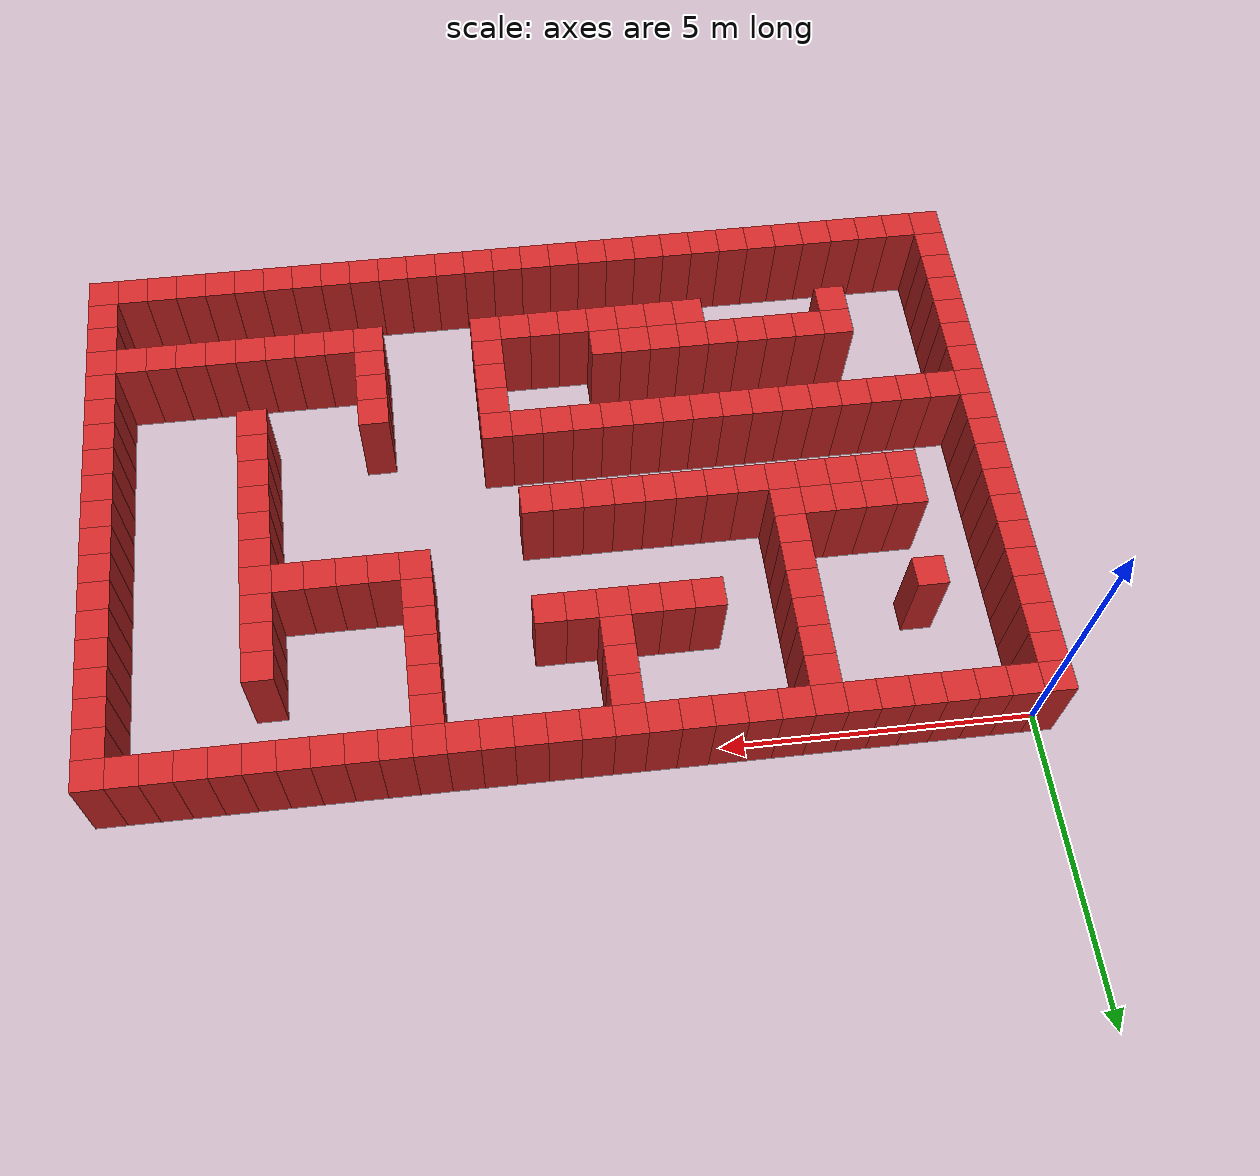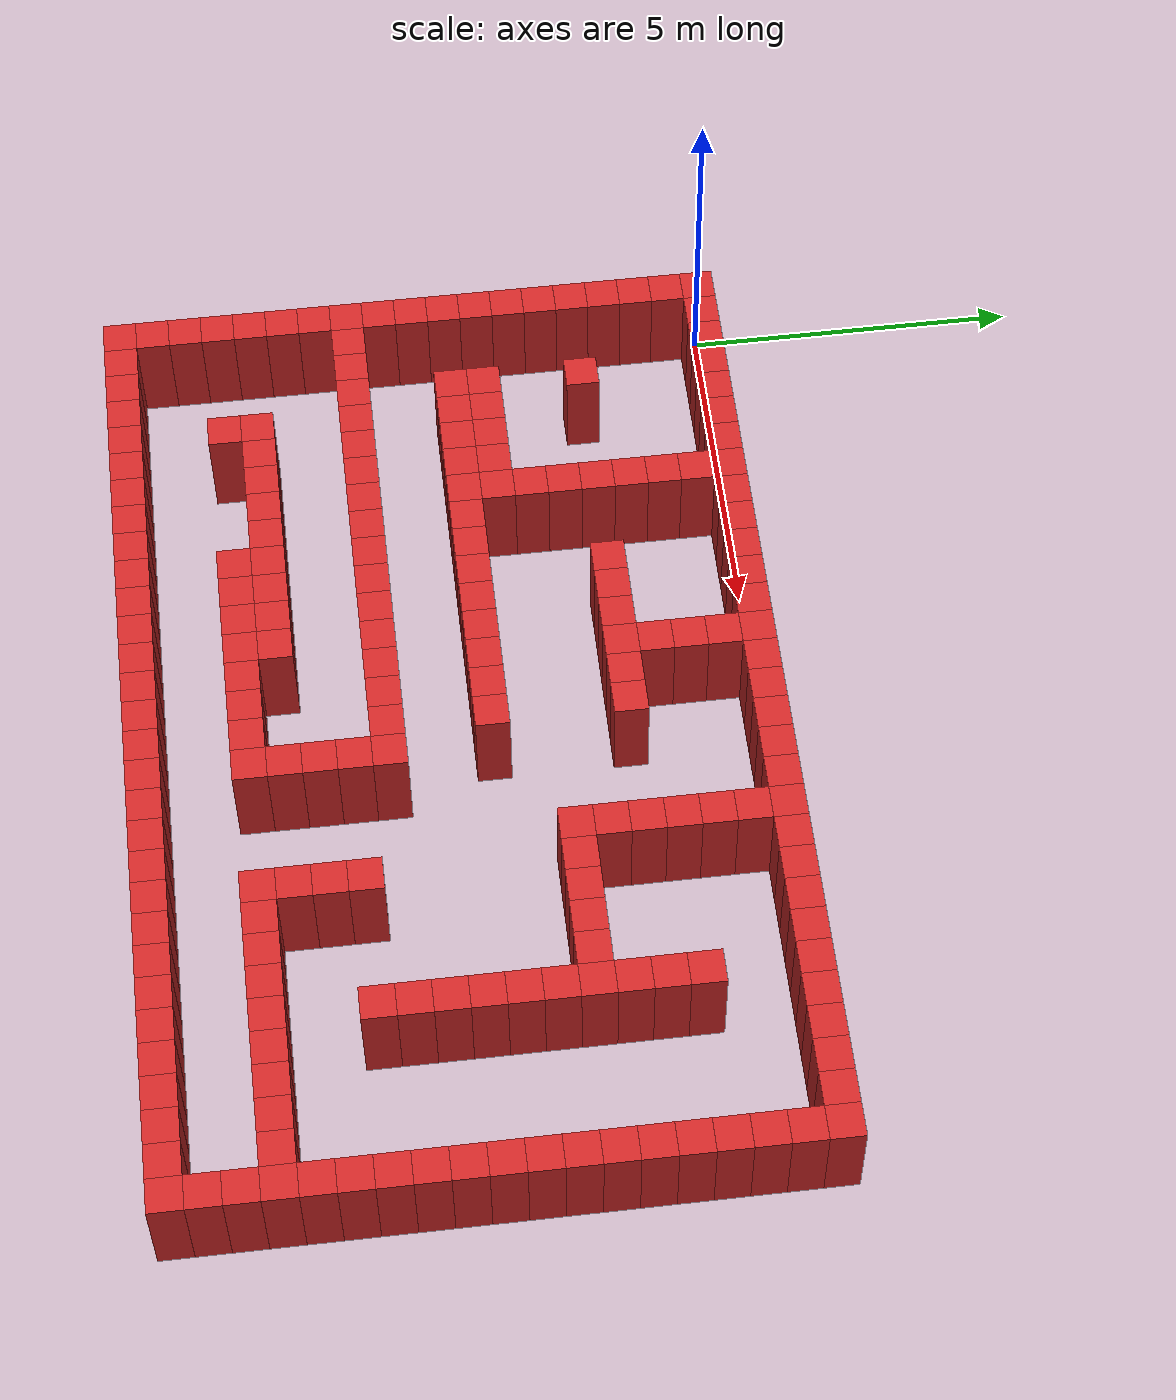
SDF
<?xml version="1.0" ?>
<sdf version="1.6">
  <model name="my_custom_world">
    <static>true</static>
    <!-- Wall 0 -->
    <link name="wall_0">
      <pose>0.0 0.0 0.75 0 0 0</pose>
      <collision name="collision">
        <geometry>
          <box>
            <size>0.5 0.5 1.5</size>
          </box>
        </geometry>
      </collision>
      <visual name="visual">
        <geometry>
          <box>
            <size>0.5 0.5 1.5</size>
          </box>
        </geometry>
        <material>
          <script>
            <uri>file://media/materials/scripts/gazebo.material</uri>
            <name>Gazebo/Red</name>
          </script>
        </material>
      </visual>
    </link>
    <!-- Wall 1 -->
    <link name="wall_1">
      <pose>0.5 0.0 0.75 0 0 0</pose>
      <collision name="collision">
        <geometry>
          <box>
            <size>0.5 0.5 1.5</size>
          </box>
        </geometry>
      </collision>
      <visual name="visual">
        <geometry>
          <box>
            <size>0.5 0.5 1.5</size>
          </box>
        </geometry>
        <material>
          <script>
            <uri>file://media/materials/scripts/gazebo.material</uri>
            <name>Gazebo/Red</name>
          </script>
        </material>
      </visual>
    </link>
    <!-- Wall 2 -->
    <link name="wall_2">
      <pose>1.0 0.0 0.75 0 0 0</pose>
      <collision name="collision">
        <geometry>
          <box>
            <size>0.5 0.5 1.5</size>
          </box>
        </geometry>
      </collision>
      <visual name="visual">
        <geometry>
          <box>
            <size>0.5 0.5 1.5</size>
          </box>
        </geometry>
        <material>
          <script>
            <uri>file://media/materials/scripts/gazebo.material</uri>
            <name>Gazebo/Red</name>
          </script>
        </material>
      </visual>
    </link>
    <!-- Wall 3 -->
    <link name="wall_3">
      <pose>1.5 0.0 0.75 0 0 0</pose>
      <collision name="collision">
        <geometry>
          <box>
            <size>0.5 0.5 1.5</size>
          </box>
        </geometry>
      </collision>
      <visual name="visual">
        <geometry>
          <box>
            <size>0.5 0.5 1.5</size>
          </box>
        </geometry>
        <material>
          <script>
            <uri>file://media/materials/scripts/gazebo.material</uri>
            <name>Gazebo/Red</name>
          </script>
        </material>
      </visual>
    </link>
    <!-- Wall 4 -->
    <link name="wall_4">
      <pose>2.0 0.0 0.75 0 0 0</pose>
      <collision name="collision">
        <geometry>
          <box>
            <size>0.5 0.5 1.5</size>
          </box>
        </geometry>
      </collision>
      <visual name="visual">
        <geometry>
          <box>
            <size>0.5 0.5 1.5</size>
          </box>
        </geometry>
        <material>
          <script>
            <uri>file://media/materials/scripts/gazebo.material</uri>
            <name>Gazebo/Red</name>
          </script>
        </material>
      </visual>
    </link>
    <!-- Wall 5 -->
    <link name="wall_5">
      <pose>2.5 0.0 0.75 0 0 0</pose>
      <collision name="collision">
        <geometry>
          <box>
            <size>0.5 0.5 1.5</size>
          </box>
        </geometry>
      </collision>
      <visual name="visual">
        <geometry>
          <box>
            <size>0.5 0.5 1.5</size>
          </box>
        </geometry>
        <material>
          <script>
            <uri>file://media/materials/scripts/gazebo.material</uri>
            <name>Gazebo/Red</name>
          </script>
        </material>
      </visual>
    </link>
    <!-- Wall 6 -->
    <link name="wall_6">
      <pose>3.0 0.0 0.75 0 0 0</pose>
      <collision name="collision">
        <geometry>
          <box>
            <size>0.5 0.5 1.5</size>
          </box>
        </geometry>
      </collision>
      <visual name="visual">
        <geometry>
          <box>
            <size>0.5 0.5 1.5</size>
          </box>
        </geometry>
        <material>
          <script>
            <uri>file://media/materials/scripts/gazebo.material</uri>
            <name>Gazebo/Red</name>
          </script>
        </material>
      </visual>
    </link>
    <!-- Wall 7 -->
    <link name="wall_7">
      <pose>3.5 0.0 0.75 0 0 0</pose>
      <collision name="collision">
        <geometry>
          <box>
            <size>0.5 0.5 1.5</size>
          </box>
        </geometry>
      </collision>
      <visual name="visual">
        <geometry>
          <box>
            <size>0.5 0.5 1.5</size>
          </box>
        </geometry>
        <material>
          <script>
            <uri>file://media/materials/scripts/gazebo.material</uri>
            <name>Gazebo/Red</name>
          </script>
        </material>
      </visual>
    </link>
    <!-- Wall 8 -->
    <link name="wall_8">
      <pose>4.0 0.0 0.75 0 0 0</pose>
      <collision name="collision">
        <geometry>
          <box>
            <size>0.5 0.5 1.5</size>
          </box>
        </geometry>
      </collision>
      <visual name="visual">
        <geometry>
          <box>
            <size>0.5 0.5 1.5</size>
          </box>
        </geometry>
        <material>
          <script>
            <uri>file://media/materials/scripts/gazebo.material</uri>
            <name>Gazebo/Red</name>
          </script>
        </material>
      </visual>
    </link>
    <!-- Wall 9 -->
    <link name="wall_9">
      <pose>4.5 0.0 0.75 0 0 0</pose>
      <collision name="collision">
        <geometry>
          <box>
            <size>0.5 0.5 1.5</size>
          </box>
        </geometry>
      </collision>
      <visual name="visual">
        <geometry>
          <box>
            <size>0.5 0.5 1.5</size>
          </box>
        </geometry>
        <material>
          <script>
            <uri>file://media/materials/scripts/gazebo.material</uri>
            <name>Gazebo/Red</name>
          </script>
        </material>
      </visual>
    </link>
    <!-- Wall 10 -->
    <link name="wall_10">
      <pose>5.0 0.0 0.75 0 0 0</pose>
      <collision name="collision">
        <geometry>
          <box>
            <size>0.5 0.5 1.5</size>
          </box>
        </geometry>
      </collision>
      <visual name="visual">
        <geometry>
          <box>
            <size>0.5 0.5 1.5</size>
          </box>
        </geometry>
        <material>
          <script>
            <uri>file://media/materials/scripts/gazebo.material</uri>
            <name>Gazebo/Red</name>
          </script>
        </material>
      </visual>
    </link>
    <!-- Wall 11 -->
    <link name="wall_11">
      <pose>5.5 0.0 0.75 0 0 0</pose>
      <collision name="collision">
        <geometry>
          <box>
            <size>0.5 0.5 1.5</size>
          </box>
        </geometry>
      </collision>
      <visual name="visual">
        <geometry>
          <box>
            <size>0.5 0.5 1.5</size>
          </box>
        </geometry>
        <material>
          <script>
            <uri>file://media/materials/scripts/gazebo.material</uri>
            <name>Gazebo/Red</name>
          </script>
        </material>
      </visual>
    </link>
    <!-- Wall 12 -->
    <link name="wall_12">
      <pose>6.0 0.0 0.75 0 0 0</pose>
      <collision name="collision">
        <geometry>
          <box>
            <size>0.5 0.5 1.5</size>
          </box>
        </geometry>
      </collision>
      <visual name="visual">
        <geometry>
          <box>
            <size>0.5 0.5 1.5</size>
          </box>
        </geometry>
        <material>
          <script>
            <uri>file://media/materials/scripts/gazebo.material</uri>
            <name>Gazebo/Red</name>
          </script>
        </material>
      </visual>
    </link>
    <!-- Wall 13 -->
    <link name="wall_13">
      <pose>6.5 0.0 0.75 0 0 0</pose>
      <collision name="collision">
        <geometry>
          <box>
            <size>0.5 0.5 1.5</size>
          </box>
        </geometry>
      </collision>
      <visual name="visual">
        <geometry>
          <box>
            <size>0.5 0.5 1.5</size>
          </box>
        </geometry>
        <material>
          <script>
            <uri>file://media/materials/scripts/gazebo.material</uri>
            <name>Gazebo/Red</name>
          </script>
        </material>
      </visual>
    </link>
    <!-- Wall 14 -->
    <link name="wall_14">
      <pose>7.0 0.0 0.75 0 0 0</pose>
      <collision name="collision">
        <geometry>
          <box>
            <size>0.5 0.5 1.5</size>
          </box>
        </geometry>
      </collision>
      <visual name="visual">
        <geometry>
          <box>
            <size>0.5 0.5 1.5</size>
          </box>
        </geometry>
        <material>
          <script>
            <uri>file://media/materials/scripts/gazebo.material</uri>
            <name>Gazebo/Red</name>
          </script>
        </material>
      </visual>
    </link>
    <!-- Wall 15 -->
    <link name="wall_15">
      <pose>7.5 0.0 0.75 0 0 0</pose>
      <collision name="collision">
        <geometry>
          <box>
            <size>0.5 0.5 1.5</size>
          </box>
        </geometry>
      </collision>
      <visual name="visual">
        <geometry>
          <box>
            <size>0.5 0.5 1.5</size>
          </box>
        </geometry>
        <material>
          <script>
            <uri>file://media/materials/scripts/gazebo.material</uri>
            <name>Gazebo/Red</name>
          </script>
        </material>
      </visual>
    </link>
    <!-- Wall 16 -->
    <link name="wall_16">
      <pose>8.0 0.0 0.75 0 0 0</pose>
      <collision name="collision">
        <geometry>
          <box>
            <size>0.5 0.5 1.5</size>
          </box>
        </geometry>
      </collision>
      <visual name="visual">
        <geometry>
          <box>
            <size>0.5 0.5 1.5</size>
          </box>
        </geometry>
        <material>
          <script>
            <uri>file://media/materials/scripts/gazebo.material</uri>
            <name>Gazebo/Red</name>
          </script>
        </material>
      </visual>
    </link>
    <!-- Wall 17 -->
    <link name="wall_17">
      <pose>8.5 0.0 0.75 0 0 0</pose>
      <collision name="collision">
        <geometry>
          <box>
            <size>0.5 0.5 1.5</size>
          </box>
        </geometry>
      </collision>
      <visual name="visual">
        <geometry>
          <box>
            <size>0.5 0.5 1.5</size>
          </box>
        </geometry>
        <material>
          <script>
            <uri>file://media/materials/scripts/gazebo.material</uri>
            <name>Gazebo/Red</name>
          </script>
        </material>
      </visual>
    </link>
    <!-- Wall 18 -->
    <link name="wall_18">
      <pose>9.0 0.0 0.75 0 0 0</pose>
      <collision name="collision">
        <geometry>
          <box>
            <size>0.5 0.5 1.5</size>
          </box>
        </geometry>
      </collision>
      <visual name="visual">
        <geometry>
          <box>
            <size>0.5 0.5 1.5</size>
          </box>
        </geometry>
        <material>
          <script>
            <uri>file://media/materials/scripts/gazebo.material</uri>
            <name>Gazebo/Red</name>
          </script>
        </material>
      </visual>
    </link>
    <!-- Wall 19 -->
    <link name="wall_19">
      <pose>9.5 0.0 0.75 0 0 0</pose>
      <collision name="collision">
        <geometry>
          <box>
            <size>0.5 0.5 1.5</size>
          </box>
        </geometry>
      </collision>
      <visual name="visual">
        <geometry>
          <box>
            <size>0.5 0.5 1.5</size>
          </box>
        </geometry>
        <material>
          <script>
            <uri>file://media/materials/scripts/gazebo.material</uri>
            <name>Gazebo/Red</name>
          </script>
        </material>
      </visual>
    </link>
    <!-- Wall 20 -->
    <link name="wall_20">
      <pose>10.0 0.0 0.75 0 0 0</pose>
      <collision name="collision">
        <geometry>
          <box>
            <size>0.5 0.5 1.5</size>
          </box>
        </geometry>
      </collision>
      <visual name="visual">
        <geometry>
          <box>
            <size>0.5 0.5 1.5</size>
          </box>
        </geometry>
        <material>
          <script>
            <uri>file://media/materials/scripts/gazebo.material</uri>
            <name>Gazebo/Red</name>
          </script>
        </material>
      </visual>
    </link>
    <!-- Wall 21 -->
    <link name="wall_21">
      <pose>10.5 0.0 0.75 0 0 0</pose>
      <collision name="collision">
        <geometry>
          <box>
            <size>0.5 0.5 1.5</size>
          </box>
        </geometry>
      </collision>
      <visual name="visual">
        <geometry>
          <box>
            <size>0.5 0.5 1.5</size>
          </box>
        </geometry>
        <material>
          <script>
            <uri>file://media/materials/scripts/gazebo.material</uri>
            <name>Gazebo/Red</name>
          </script>
        </material>
      </visual>
    </link>
    <!-- Wall 22 -->
    <link name="wall_22">
      <pose>11.0 0.0 0.75 0 0 0</pose>
      <collision name="collision">
        <geometry>
          <box>
            <size>0.5 0.5 1.5</size>
          </box>
        </geometry>
      </collision>
      <visual name="visual">
        <geometry>
          <box>
            <size>0.5 0.5 1.5</size>
          </box>
        </geometry>
        <material>
          <script>
            <uri>file://media/materials/scripts/gazebo.material</uri>
            <name>Gazebo/Red</name>
          </script>
        </material>
      </visual>
    </link>
    <!-- Wall 23 -->
    <link name="wall_23">
      <pose>11.5 0.0 0.75 0 0 0</pose>
      <collision name="collision">
        <geometry>
          <box>
            <size>0.5 0.5 1.5</size>
          </box>
        </geometry>
      </collision>
      <visual name="visual">
        <geometry>
          <box>
            <size>0.5 0.5 1.5</size>
          </box>
        </geometry>
        <material>
          <script>
            <uri>file://media/materials/scripts/gazebo.material</uri>
            <name>Gazebo/Red</name>
          </script>
        </material>
      </visual>
    </link>
    <!-- Wall 24 -->
    <link name="wall_24">
      <pose>12.0 0.0 0.75 0 0 0</pose>
      <collision name="collision">
        <geometry>
          <box>
            <size>0.5 0.5 1.5</size>
          </box>
        </geometry>
      </collision>
      <visual name="visual">
        <geometry>
          <box>
            <size>0.5 0.5 1.5</size>
          </box>
        </geometry>
        <material>
          <script>
            <uri>file://media/materials/scripts/gazebo.material</uri>
            <name>Gazebo/Red</name>
          </script>
        </material>
      </visual>
    </link>
    <!-- Wall 25 -->
    <link name="wall_25">
      <pose>12.5 0.0 0.75 0 0 0</pose>
      <collision name="collision">
        <geometry>
          <box>
            <size>0.5 0.5 1.5</size>
          </box>
        </geometry>
      </collision>
      <visual name="visual">
        <geometry>
          <box>
            <size>0.5 0.5 1.5</size>
          </box>
        </geometry>
        <material>
          <script>
            <uri>file://media/materials/scripts/gazebo.material</uri>
            <name>Gazebo/Red</name>
          </script>
        </material>
      </visual>
    </link>
    <!-- Wall 26 -->
    <link name="wall_26">
      <pose>13.0 0.0 0.75 0 0 0</pose>
      <collision name="collision">
        <geometry>
          <box>
            <size>0.5 0.5 1.5</size>
          </box>
        </geometry>
      </collision>
      <visual name="visual">
        <geometry>
          <box>
            <size>0.5 0.5 1.5</size>
          </box>
        </geometry>
        <material>
          <script>
            <uri>file://media/materials/scripts/gazebo.material</uri>
            <name>Gazebo/Red</name>
          </script>
        </material>
      </visual>
    </link>
    <!-- Wall 27 -->
    <link name="wall_27">
      <pose>13.5 0.0 0.75 0 0 0</pose>
      <collision name="collision">
        <geometry>
          <box>
            <size>0.5 0.5 1.5</size>
          </box>
        </geometry>
      </collision>
      <visual name="visual">
        <geometry>
          <box>
            <size>0.5 0.5 1.5</size>
          </box>
        </geometry>
        <material>
          <script>
            <uri>file://media/materials/scripts/gazebo.material</uri>
            <name>Gazebo/Red</name>
          </script>
        </material>
      </visual>
    </link>
    <!-- Wall 28 -->
    <link name="wall_28">
      <pose>14.0 0.0 0.75 0 0 0</pose>
      <collision name="collision">
        <geometry>
          <box>
            <size>0.5 0.5 1.5</size>
          </box>
        </geometry>
      </collision>
      <visual name="visual">
        <geometry>
          <box>
            <size>0.5 0.5 1.5</size>
          </box>
        </geometry>
        <material>
          <script>
            <uri>file://media/materials/scripts/gazebo.material</uri>
            <name>Gazebo/Red</name>
          </script>
        </material>
      </visual>
    </link>
    <!-- Wall 29 -->
    <link name="wall_29">
      <pose>14.5 0.0 0.75 0 0 0</pose>
      <collision name="collision">
        <geometry>
          <box>
            <size>0.5 0.5 1.5</size>
          </box>
        </geometry>
      </collision>
      <visual name="visual">
        <geometry>
          <box>
            <size>0.5 0.5 1.5</size>
          </box>
        </geometry>
        <material>
          <script>
            <uri>file://media/materials/scripts/gazebo.material</uri>
            <name>Gazebo/Red</name>
          </script>
        </material>
      </visual>
    </link>
    <!-- Wall 30 -->
    <link name="wall_30">
      <pose>0.0 -0.5 0.75 0 0 0</pose>
      <collision name="collision">
        <geometry>
          <box>
            <size>0.5 0.5 1.5</size>
          </box>
        </geometry>
      </collision>
      <visual name="visual">
        <geometry>
          <box>
            <size>0.5 0.5 1.5</size>
          </box>
        </geometry>
        <material>
          <script>
            <uri>file://media/materials/scripts/gazebo.material</uri>
            <name>Gazebo/Red</name>
          </script>
        </material>
      </visual>
    </link>
    <!-- Wall 31 -->
    <link name="wall_31">
      <pose>3.5 -0.5 0.75 0 0 0</pose>
      <collision name="collision">
        <geometry>
          <box>
            <size>0.5 0.5 1.5</size>
          </box>
        </geometry>
      </collision>
      <visual name="visual">
        <geometry>
          <box>
            <size>0.5 0.5 1.5</size>
          </box>
        </geometry>
        <material>
          <script>
            <uri>file://media/materials/scripts/gazebo.material</uri>
            <name>Gazebo/Red</name>
          </script>
        </material>
      </visual>
    </link>
    <!-- Wall 32 -->
    <link name="wall_32">
      <pose>6.5 -0.5 0.75 0 0 0</pose>
      <collision name="collision">
        <geometry>
          <box>
            <size>0.5 0.5 1.5</size>
          </box>
        </geometry>
      </collision>
      <visual name="visual">
        <geometry>
          <box>
            <size>0.5 0.5 1.5</size>
          </box>
        </geometry>
        <material>
          <script>
            <uri>file://media/materials/scripts/gazebo.material</uri>
            <name>Gazebo/Red</name>
          </script>
        </material>
      </visual>
    </link>
    <!-- Wall 33 -->
    <link name="wall_33">
      <pose>9.5 -0.5 0.75 0 0 0</pose>
      <collision name="collision">
        <geometry>
          <box>
            <size>0.5 0.5 1.5</size>
          </box>
        </geometry>
      </collision>
      <visual name="visual">
        <geometry>
          <box>
            <size>0.5 0.5 1.5</size>
          </box>
        </geometry>
        <material>
          <script>
            <uri>file://media/materials/scripts/gazebo.material</uri>
            <name>Gazebo/Red</name>
          </script>
        </material>
      </visual>
    </link>
    <!-- Wall 34 -->
    <link name="wall_34">
      <pose>14.5 -0.5 0.75 0 0 0</pose>
      <collision name="collision">
        <geometry>
          <box>
            <size>0.5 0.5 1.5</size>
          </box>
        </geometry>
      </collision>
      <visual name="visual">
        <geometry>
          <box>
            <size>0.5 0.5 1.5</size>
          </box>
        </geometry>
        <material>
          <script>
            <uri>file://media/materials/scripts/gazebo.material</uri>
            <name>Gazebo/Red</name>
          </script>
        </material>
      </visual>
    </link>
    <!-- Wall 35 -->
    <link name="wall_35">
      <pose>0.0 -1.0 0.75 0 0 0</pose>
      <collision name="collision">
        <geometry>
          <box>
            <size>0.5 0.5 1.5</size>
          </box>
        </geometry>
      </collision>
      <visual name="visual">
        <geometry>
          <box>
            <size>0.5 0.5 1.5</size>
          </box>
        </geometry>
        <material>
          <script>
            <uri>file://media/materials/scripts/gazebo.material</uri>
            <name>Gazebo/Red</name>
          </script>
        </material>
      </visual>
    </link>
    <!-- Wall 36 -->
    <link name="wall_36">
      <pose>3.5 -1.0 0.75 0 0 0</pose>
      <collision name="collision">
        <geometry>
          <box>
            <size>0.5 0.5 1.5</size>
          </box>
        </geometry>
      </collision>
      <visual name="visual">
        <geometry>
          <box>
            <size>0.5 0.5 1.5</size>
          </box>
        </geometry>
        <material>
          <script>
            <uri>file://media/materials/scripts/gazebo.material</uri>
            <name>Gazebo/Red</name>
          </script>
        </material>
      </visual>
    </link>
    <!-- Wall 37 -->
    <link name="wall_37">
      <pose>6.5 -1.0 0.75 0 0 0</pose>
      <collision name="collision">
        <geometry>
          <box>
            <size>0.5 0.5 1.5</size>
          </box>
        </geometry>
      </collision>
      <visual name="visual">
        <geometry>
          <box>
            <size>0.5 0.5 1.5</size>
          </box>
        </geometry>
        <material>
          <script>
            <uri>file://media/materials/scripts/gazebo.material</uri>
            <name>Gazebo/Red</name>
          </script>
        </material>
      </visual>
    </link>
    <!-- Wall 38 -->
    <link name="wall_38">
      <pose>9.5 -1.0 0.75 0 0 0</pose>
      <collision name="collision">
        <geometry>
          <box>
            <size>0.5 0.5 1.5</size>
          </box>
        </geometry>
      </collision>
      <visual name="visual">
        <geometry>
          <box>
            <size>0.5 0.5 1.5</size>
          </box>
        </geometry>
        <material>
          <script>
            <uri>file://media/materials/scripts/gazebo.material</uri>
            <name>Gazebo/Red</name>
          </script>
        </material>
      </visual>
    </link>
    <!-- Wall 39 -->
    <link name="wall_39">
      <pose>14.5 -1.0 0.75 0 0 0</pose>
      <collision name="collision">
        <geometry>
          <box>
            <size>0.5 0.5 1.5</size>
          </box>
        </geometry>
      </collision>
      <visual name="visual">
        <geometry>
          <box>
            <size>0.5 0.5 1.5</size>
          </box>
        </geometry>
        <material>
          <script>
            <uri>file://media/materials/scripts/gazebo.material</uri>
            <name>Gazebo/Red</name>
          </script>
        </material>
      </visual>
    </link>
    <!-- Wall 40 -->
    <link name="wall_40">
      <pose>0.0 -1.5 0.75 0 0 0</pose>
      <collision name="collision">
        <geometry>
          <box>
            <size>0.5 0.5 1.5</size>
          </box>
        </geometry>
      </collision>
      <visual name="visual">
        <geometry>
          <box>
            <size>0.5 0.5 1.5</size>
          </box>
        </geometry>
        <material>
          <script>
            <uri>file://media/materials/scripts/gazebo.material</uri>
            <name>Gazebo/Red</name>
          </script>
        </material>
      </visual>
    </link>
    <!-- Wall 41 -->
    <link name="wall_41">
      <pose>3.5 -1.5 0.75 0 0 0</pose>
      <collision name="collision">
        <geometry>
          <box>
            <size>0.5 0.5 1.5</size>
          </box>
        </geometry>
      </collision>
      <visual name="visual">
        <geometry>
          <box>
            <size>0.5 0.5 1.5</size>
          </box>
        </geometry>
        <material>
          <script>
            <uri>file://media/materials/scripts/gazebo.material</uri>
            <name>Gazebo/Red</name>
          </script>
        </material>
      </visual>
    </link>
    <!-- Wall 42 -->
    <link name="wall_42">
      <pose>6.5 -1.5 0.75 0 0 0</pose>
      <collision name="collision">
        <geometry>
          <box>
            <size>0.5 0.5 1.5</size>
          </box>
        </geometry>
      </collision>
      <visual name="visual">
        <geometry>
          <box>
            <size>0.5 0.5 1.5</size>
          </box>
        </geometry>
        <material>
          <script>
            <uri>file://media/materials/scripts/gazebo.material</uri>
            <name>Gazebo/Red</name>
          </script>
        </material>
      </visual>
    </link>
    <!-- Wall 43 -->
    <link name="wall_43">
      <pose>9.5 -1.5 0.75 0 0 0</pose>
      <collision name="collision">
        <geometry>
          <box>
            <size>0.5 0.5 1.5</size>
          </box>
        </geometry>
      </collision>
      <visual name="visual">
        <geometry>
          <box>
            <size>0.5 0.5 1.5</size>
          </box>
        </geometry>
        <material>
          <script>
            <uri>file://media/materials/scripts/gazebo.material</uri>
            <name>Gazebo/Red</name>
          </script>
        </material>
      </visual>
    </link>
    <!-- Wall 44 -->
    <link name="wall_44">
      <pose>12.0 -1.5 0.75 0 0 0</pose>
      <collision name="collision">
        <geometry>
          <box>
            <size>0.5 0.5 1.5</size>
          </box>
        </geometry>
      </collision>
      <visual name="visual">
        <geometry>
          <box>
            <size>0.5 0.5 1.5</size>
          </box>
        </geometry>
        <material>
          <script>
            <uri>file://media/materials/scripts/gazebo.material</uri>
            <name>Gazebo/Red</name>
          </script>
        </material>
      </visual>
    </link>
    <!-- Wall 45 -->
    <link name="wall_45">
      <pose>14.5 -1.5 0.75 0 0 0</pose>
      <collision name="collision">
        <geometry>
          <box>
            <size>0.5 0.5 1.5</size>
          </box>
        </geometry>
      </collision>
      <visual name="visual">
        <geometry>
          <box>
            <size>0.5 0.5 1.5</size>
          </box>
        </geometry>
        <material>
          <script>
            <uri>file://media/materials/scripts/gazebo.material</uri>
            <name>Gazebo/Red</name>
          </script>
        </material>
      </visual>
    </link>
    <!-- Wall 46 -->
    <link name="wall_46">
      <pose>0.0 -2.0 0.75 0 0 0</pose>
      <collision name="collision">
        <geometry>
          <box>
            <size>0.5 0.5 1.5</size>
          </box>
        </geometry>
      </collision>
      <visual name="visual">
        <geometry>
          <box>
            <size>0.5 0.5 1.5</size>
          </box>
        </geometry>
        <material>
          <script>
            <uri>file://media/materials/scripts/gazebo.material</uri>
            <name>Gazebo/Red</name>
          </script>
        </material>
      </visual>
    </link>
    <!-- Wall 47 -->
    <link name="wall_47">
      <pose>1.5 -2.0 0.75 0 0 0</pose>
      <collision name="collision">
        <geometry>
          <box>
            <size>0.5 0.5 1.5</size>
          </box>
        </geometry>
      </collision>
      <visual name="visual">
        <geometry>
          <box>
            <size>0.5 0.5 1.5</size>
          </box>
        </geometry>
        <material>
          <script>
            <uri>file://media/materials/scripts/gazebo.material</uri>
            <name>Gazebo/Red</name>
          </script>
        </material>
      </visual>
    </link>
    <!-- Wall 48 -->
    <link name="wall_48">
      <pose>3.5 -2.0 0.75 0 0 0</pose>
      <collision name="collision">
        <geometry>
          <box>
            <size>0.5 0.5 1.5</size>
          </box>
        </geometry>
      </collision>
      <visual name="visual">
        <geometry>
          <box>
            <size>0.5 0.5 1.5</size>
          </box>
        </geometry>
        <material>
          <script>
            <uri>file://media/materials/scripts/gazebo.material</uri>
            <name>Gazebo/Red</name>
          </script>
        </material>
      </visual>
    </link>
    <!-- Wall 49 -->
    <link name="wall_49">
      <pose>5.0 -2.0 0.75 0 0 0</pose>
      <collision name="collision">
        <geometry>
          <box>
            <size>0.5 0.5 1.5</size>
          </box>
        </geometry>
      </collision>
      <visual name="visual">
        <geometry>
          <box>
            <size>0.5 0.5 1.5</size>
          </box>
        </geometry>
        <material>
          <script>
            <uri>file://media/materials/scripts/gazebo.material</uri>
            <name>Gazebo/Red</name>
          </script>
        </material>
      </visual>
    </link>
    <!-- Wall 50 -->
    <link name="wall_50">
      <pose>5.5 -2.0 0.75 0 0 0</pose>
      <collision name="collision">
        <geometry>
          <box>
            <size>0.5 0.5 1.5</size>
          </box>
        </geometry>
      </collision>
      <visual name="visual">
        <geometry>
          <box>
            <size>0.5 0.5 1.5</size>
          </box>
        </geometry>
        <material>
          <script>
            <uri>file://media/materials/scripts/gazebo.material</uri>
            <name>Gazebo/Red</name>
          </script>
        </material>
      </visual>
    </link>
    <!-- Wall 51 -->
    <link name="wall_51">
      <pose>6.0 -2.0 0.75 0 0 0</pose>
      <collision name="collision">
        <geometry>
          <box>
            <size>0.5 0.5 1.5</size>
          </box>
        </geometry>
      </collision>
      <visual name="visual">
        <geometry>
          <box>
            <size>0.5 0.5 1.5</size>
          </box>
        </geometry>
        <material>
          <script>
            <uri>file://media/materials/scripts/gazebo.material</uri>
            <name>Gazebo/Red</name>
          </script>
        </material>
      </visual>
    </link>
    <!-- Wall 52 -->
    <link name="wall_52">
      <pose>6.5 -2.0 0.75 0 0 0</pose>
      <collision name="collision">
        <geometry>
          <box>
            <size>0.5 0.5 1.5</size>
          </box>
        </geometry>
      </collision>
      <visual name="visual">
        <geometry>
          <box>
            <size>0.5 0.5 1.5</size>
          </box>
        </geometry>
        <material>
          <script>
            <uri>file://media/materials/scripts/gazebo.material</uri>
            <name>Gazebo/Red</name>
          </script>
        </material>
      </visual>
    </link>
    <!-- Wall 53 -->
    <link name="wall_53">
      <pose>7.0 -2.0 0.75 0 0 0</pose>
      <collision name="collision">
        <geometry>
          <box>
            <size>0.5 0.5 1.5</size>
          </box>
        </geometry>
      </collision>
      <visual name="visual">
        <geometry>
          <box>
            <size>0.5 0.5 1.5</size>
          </box>
        </geometry>
        <material>
          <script>
            <uri>file://media/materials/scripts/gazebo.material</uri>
            <name>Gazebo/Red</name>
          </script>
        </material>
      </visual>
    </link>
    <!-- Wall 54 -->
    <link name="wall_54">
      <pose>7.5 -2.0 0.75 0 0 0</pose>
      <collision name="collision">
        <geometry>
          <box>
            <size>0.5 0.5 1.5</size>
          </box>
        </geometry>
      </collision>
      <visual name="visual">
        <geometry>
          <box>
            <size>0.5 0.5 1.5</size>
          </box>
        </geometry>
        <material>
          <script>
            <uri>file://media/materials/scripts/gazebo.material</uri>
            <name>Gazebo/Red</name>
          </script>
        </material>
      </visual>
    </link>
    <!-- Wall 55 -->
    <link name="wall_55">
      <pose>9.5 -2.0 0.75 0 0 0</pose>
      <collision name="collision">
        <geometry>
          <box>
            <size>0.5 0.5 1.5</size>
          </box>
        </geometry>
      </collision>
      <visual name="visual">
        <geometry>
          <box>
            <size>0.5 0.5 1.5</size>
          </box>
        </geometry>
        <material>
          <script>
            <uri>file://media/materials/scripts/gazebo.material</uri>
            <name>Gazebo/Red</name>
          </script>
        </material>
      </visual>
    </link>
    <!-- Wall 56 -->
    <link name="wall_56">
      <pose>12.0 -2.0 0.75 0 0 0</pose>
      <collision name="collision">
        <geometry>
          <box>
            <size>0.5 0.5 1.5</size>
          </box>
        </geometry>
      </collision>
      <visual name="visual">
        <geometry>
          <box>
            <size>0.5 0.5 1.5</size>
          </box>
        </geometry>
        <material>
          <script>
            <uri>file://media/materials/scripts/gazebo.material</uri>
            <name>Gazebo/Red</name>
          </script>
        </material>
      </visual>
    </link>
    <!-- Wall 57 -->
    <link name="wall_57">
      <pose>14.5 -2.0 0.75 0 0 0</pose>
      <collision name="collision">
        <geometry>
          <box>
            <size>0.5 0.5 1.5</size>
          </box>
        </geometry>
      </collision>
      <visual name="visual">
        <geometry>
          <box>
            <size>0.5 0.5 1.5</size>
          </box>
        </geometry>
        <material>
          <script>
            <uri>file://media/materials/scripts/gazebo.material</uri>
            <name>Gazebo/Red</name>
          </script>
        </material>
      </visual>
    </link>
    <!-- Wall 58 -->
    <link name="wall_58">
      <pose>0.0 -2.5 0.75 0 0 0</pose>
      <collision name="collision">
        <geometry>
          <box>
            <size>0.5 0.5 1.5</size>
          </box>
        </geometry>
      </collision>
      <visual name="visual">
        <geometry>
          <box>
            <size>0.5 0.5 1.5</size>
          </box>
        </geometry>
        <material>
          <script>
            <uri>file://media/materials/scripts/gazebo.material</uri>
            <name>Gazebo/Red</name>
          </script>
        </material>
      </visual>
    </link>
    <!-- Wall 59 -->
    <link name="wall_59">
      <pose>3.5 -2.5 0.75 0 0 0</pose>
      <collision name="collision">
        <geometry>
          <box>
            <size>0.5 0.5 1.5</size>
          </box>
        </geometry>
      </collision>
      <visual name="visual">
        <geometry>
          <box>
            <size>0.5 0.5 1.5</size>
          </box>
        </geometry>
        <material>
          <script>
            <uri>file://media/materials/scripts/gazebo.material</uri>
            <name>Gazebo/Red</name>
          </script>
        </material>
      </visual>
    </link>
    <!-- Wall 60 -->
    <link name="wall_60">
      <pose>9.5 -2.5 0.75 0 0 0</pose>
      <collision name="collision">
        <geometry>
          <box>
            <size>0.5 0.5 1.5</size>
          </box>
        </geometry>
      </collision>
      <visual name="visual">
        <geometry>
          <box>
            <size>0.5 0.5 1.5</size>
          </box>
        </geometry>
        <material>
          <script>
            <uri>file://media/materials/scripts/gazebo.material</uri>
            <name>Gazebo/Red</name>
          </script>
        </material>
      </visual>
    </link>
    <!-- Wall 61 -->
    <link name="wall_61">
      <pose>12.0 -2.5 0.75 0 0 0</pose>
      <collision name="collision">
        <geometry>
          <box>
            <size>0.5 0.5 1.5</size>
          </box>
        </geometry>
      </collision>
      <visual name="visual">
        <geometry>
          <box>
            <size>0.5 0.5 1.5</size>
          </box>
        </geometry>
        <material>
          <script>
            <uri>file://media/materials/scripts/gazebo.material</uri>
            <name>Gazebo/Red</name>
          </script>
        </material>
      </visual>
    </link>
    <!-- Wall 62 -->
    <link name="wall_62">
      <pose>14.5 -2.5 0.75 0 0 0</pose>
      <collision name="collision">
        <geometry>
          <box>
            <size>0.5 0.5 1.5</size>
          </box>
        </geometry>
      </collision>
      <visual name="visual">
        <geometry>
          <box>
            <size>0.5 0.5 1.5</size>
          </box>
        </geometry>
        <material>
          <script>
            <uri>file://media/materials/scripts/gazebo.material</uri>
            <name>Gazebo/Red</name>
          </script>
        </material>
      </visual>
    </link>
    <!-- Wall 63 -->
    <link name="wall_63">
      <pose>0.0 -3.0 0.75 0 0 0</pose>
      <collision name="collision">
        <geometry>
          <box>
            <size>0.5 0.5 1.5</size>
          </box>
        </geometry>
      </collision>
      <visual name="visual">
        <geometry>
          <box>
            <size>0.5 0.5 1.5</size>
          </box>
        </geometry>
        <material>
          <script>
            <uri>file://media/materials/scripts/gazebo.material</uri>
            <name>Gazebo/Red</name>
          </script>
        </material>
      </visual>
    </link>
    <!-- Wall 64 -->
    <link name="wall_64">
      <pose>3.5 -3.0 0.75 0 0 0</pose>
      <collision name="collision">
        <geometry>
          <box>
            <size>0.5 0.5 1.5</size>
          </box>
        </geometry>
      </collision>
      <visual name="visual">
        <geometry>
          <box>
            <size>0.5 0.5 1.5</size>
          </box>
        </geometry>
        <material>
          <script>
            <uri>file://media/materials/scripts/gazebo.material</uri>
            <name>Gazebo/Red</name>
          </script>
        </material>
      </visual>
    </link>
    <!-- Wall 65 -->
    <link name="wall_65">
      <pose>9.5 -3.0 0.75 0 0 0</pose>
      <collision name="collision">
        <geometry>
          <box>
            <size>0.5 0.5 1.5</size>
          </box>
        </geometry>
      </collision>
      <visual name="visual">
        <geometry>
          <box>
            <size>0.5 0.5 1.5</size>
          </box>
        </geometry>
        <material>
          <script>
            <uri>file://media/materials/scripts/gazebo.material</uri>
            <name>Gazebo/Red</name>
          </script>
        </material>
      </visual>
    </link>
    <!-- Wall 66 -->
    <link name="wall_66">
      <pose>10.0 -3.0 0.75 0 0 0</pose>
      <collision name="collision">
        <geometry>
          <box>
            <size>0.5 0.5 1.5</size>
          </box>
        </geometry>
      </collision>
      <visual name="visual">
        <geometry>
          <box>
            <size>0.5 0.5 1.5</size>
          </box>
        </geometry>
        <material>
          <script>
            <uri>file://media/materials/scripts/gazebo.material</uri>
            <name>Gazebo/Red</name>
          </script>
        </material>
      </visual>
    </link>
    <!-- Wall 67 -->
    <link name="wall_67">
      <pose>10.5 -3.0 0.75 0 0 0</pose>
      <collision name="collision">
        <geometry>
          <box>
            <size>0.5 0.5 1.5</size>
          </box>
        </geometry>
      </collision>
      <visual name="visual">
        <geometry>
          <box>
            <size>0.5 0.5 1.5</size>
          </box>
        </geometry>
        <material>
          <script>
            <uri>file://media/materials/scripts/gazebo.material</uri>
            <name>Gazebo/Red</name>
          </script>
        </material>
      </visual>
    </link>
    <!-- Wall 68 -->
    <link name="wall_68">
      <pose>11.0 -3.0 0.75 0 0 0</pose>
      <collision name="collision">
        <geometry>
          <box>
            <size>0.5 0.5 1.5</size>
          </box>
        </geometry>
      </collision>
      <visual name="visual">
        <geometry>
          <box>
            <size>0.5 0.5 1.5</size>
          </box>
        </geometry>
        <material>
          <script>
            <uri>file://media/materials/scripts/gazebo.material</uri>
            <name>Gazebo/Red</name>
          </script>
        </material>
      </visual>
    </link>
    <!-- Wall 69 -->
    <link name="wall_69">
      <pose>11.5 -3.0 0.75 0 0 0</pose>
      <collision name="collision">
        <geometry>
          <box>
            <size>0.5 0.5 1.5</size>
          </box>
        </geometry>
      </collision>
      <visual name="visual">
        <geometry>
          <box>
            <size>0.5 0.5 1.5</size>
          </box>
        </geometry>
        <material>
          <script>
            <uri>file://media/materials/scripts/gazebo.material</uri>
            <name>Gazebo/Red</name>
          </script>
        </material>
      </visual>
    </link>
    <!-- Wall 70 -->
    <link name="wall_70">
      <pose>12.0 -3.0 0.75 0 0 0</pose>
      <collision name="collision">
        <geometry>
          <box>
            <size>0.5 0.5 1.5</size>
          </box>
        </geometry>
      </collision>
      <visual name="visual">
        <geometry>
          <box>
            <size>0.5 0.5 1.5</size>
          </box>
        </geometry>
        <material>
          <script>
            <uri>file://media/materials/scripts/gazebo.material</uri>
            <name>Gazebo/Red</name>
          </script>
        </material>
      </visual>
    </link>
    <!-- Wall 71 -->
    <link name="wall_71">
      <pose>14.5 -3.0 0.75 0 0 0</pose>
      <collision name="collision">
        <geometry>
          <box>
            <size>0.5 0.5 1.5</size>
          </box>
        </geometry>
      </collision>
      <visual name="visual">
        <geometry>
          <box>
            <size>0.5 0.5 1.5</size>
          </box>
        </geometry>
        <material>
          <script>
            <uri>file://media/materials/scripts/gazebo.material</uri>
            <name>Gazebo/Red</name>
          </script>
        </material>
      </visual>
    </link>
    <!-- Wall 72 -->
    <link name="wall_72">
      <pose>0.0 -3.5 0.75 0 0 0</pose>
      <collision name="collision">
        <geometry>
          <box>
            <size>0.5 0.5 1.5</size>
          </box>
        </geometry>
      </collision>
      <visual name="visual">
        <geometry>
          <box>
            <size>0.5 0.5 1.5</size>
          </box>
        </geometry>
        <material>
          <script>
            <uri>file://media/materials/scripts/gazebo.material</uri>
            <name>Gazebo/Red</name>
          </script>
        </material>
      </visual>
    </link>
    <!-- Wall 73 -->
    <link name="wall_73">
      <pose>1.5 -3.5 0.75 0 0 0</pose>
      <collision name="collision">
        <geometry>
          <box>
            <size>0.5 0.5 1.5</size>
          </box>
        </geometry>
      </collision>
      <visual name="visual">
        <geometry>
          <box>
            <size>0.5 0.5 1.5</size>
          </box>
        </geometry>
        <material>
          <script>
            <uri>file://media/materials/scripts/gazebo.material</uri>
            <name>Gazebo/Red</name>
          </script>
        </material>
      </visual>
    </link>
    <!-- Wall 74 -->
    <link name="wall_74">
      <pose>2.0 -3.5 0.75 0 0 0</pose>
      <collision name="collision">
        <geometry>
          <box>
            <size>0.5 0.5 1.5</size>
          </box>
        </geometry>
      </collision>
      <visual name="visual">
        <geometry>
          <box>
            <size>0.5 0.5 1.5</size>
          </box>
        </geometry>
        <material>
          <script>
            <uri>file://media/materials/scripts/gazebo.material</uri>
            <name>Gazebo/Red</name>
          </script>
        </material>
      </visual>
    </link>
    <!-- Wall 75 -->
    <link name="wall_75">
      <pose>2.5 -3.5 0.75 0 0 0</pose>
      <collision name="collision">
        <geometry>
          <box>
            <size>0.5 0.5 1.5</size>
          </box>
        </geometry>
      </collision>
      <visual name="visual">
        <geometry>
          <box>
            <size>0.5 0.5 1.5</size>
          </box>
        </geometry>
        <material>
          <script>
            <uri>file://media/materials/scripts/gazebo.material</uri>
            <name>Gazebo/Red</name>
          </script>
        </material>
      </visual>
    </link>
    <!-- Wall 76 -->
    <link name="wall_76">
      <pose>3.0 -3.5 0.75 0 0 0</pose>
      <collision name="collision">
        <geometry>
          <box>
            <size>0.5 0.5 1.5</size>
          </box>
        </geometry>
      </collision>
      <visual name="visual">
        <geometry>
          <box>
            <size>0.5 0.5 1.5</size>
          </box>
        </geometry>
        <material>
          <script>
            <uri>file://media/materials/scripts/gazebo.material</uri>
            <name>Gazebo/Red</name>
          </script>
        </material>
      </visual>
    </link>
    <!-- Wall 77 -->
    <link name="wall_77">
      <pose>3.5 -3.5 0.75 0 0 0</pose>
      <collision name="collision">
        <geometry>
          <box>
            <size>0.5 0.5 1.5</size>
          </box>
        </geometry>
      </collision>
      <visual name="visual">
        <geometry>
          <box>
            <size>0.5 0.5 1.5</size>
          </box>
        </geometry>
        <material>
          <script>
            <uri>file://media/materials/scripts/gazebo.material</uri>
            <name>Gazebo/Red</name>
          </script>
        </material>
      </visual>
    </link>
    <!-- Wall 78 -->
    <link name="wall_78">
      <pose>12.0 -3.5 0.75 0 0 0</pose>
      <collision name="collision">
        <geometry>
          <box>
            <size>0.5 0.5 1.5</size>
          </box>
        </geometry>
      </collision>
      <visual name="visual">
        <geometry>
          <box>
            <size>0.5 0.5 1.5</size>
          </box>
        </geometry>
        <material>
          <script>
            <uri>file://media/materials/scripts/gazebo.material</uri>
            <name>Gazebo/Red</name>
          </script>
        </material>
      </visual>
    </link>
    <!-- Wall 79 -->
    <link name="wall_79">
      <pose>14.5 -3.5 0.75 0 0 0</pose>
      <collision name="collision">
        <geometry>
          <box>
            <size>0.5 0.5 1.5</size>
          </box>
        </geometry>
      </collision>
      <visual name="visual">
        <geometry>
          <box>
            <size>0.5 0.5 1.5</size>
          </box>
        </geometry>
        <material>
          <script>
            <uri>file://media/materials/scripts/gazebo.material</uri>
            <name>Gazebo/Red</name>
          </script>
        </material>
      </visual>
    </link>
    <!-- Wall 80 -->
    <link name="wall_80">
      <pose>0.0 -4.0 0.75 0 0 0</pose>
      <collision name="collision">
        <geometry>
          <box>
            <size>0.5 0.5 1.5</size>
          </box>
        </geometry>
      </collision>
      <visual name="visual">
        <geometry>
          <box>
            <size>0.5 0.5 1.5</size>
          </box>
        </geometry>
        <material>
          <script>
            <uri>file://media/materials/scripts/gazebo.material</uri>
            <name>Gazebo/Red</name>
          </script>
        </material>
      </visual>
    </link>
    <!-- Wall 81 -->
    <link name="wall_81">
      <pose>1.5 -4.0 0.75 0 0 0</pose>
      <collision name="collision">
        <geometry>
          <box>
            <size>0.5 0.5 1.5</size>
          </box>
        </geometry>
      </collision>
      <visual name="visual">
        <geometry>
          <box>
            <size>0.5 0.5 1.5</size>
          </box>
        </geometry>
        <material>
          <script>
            <uri>file://media/materials/scripts/gazebo.material</uri>
            <name>Gazebo/Red</name>
          </script>
        </material>
      </visual>
    </link>
    <!-- Wall 82 -->
    <link name="wall_82">
      <pose>2.0 -4.0 0.75 0 0 0</pose>
      <collision name="collision">
        <geometry>
          <box>
            <size>0.5 0.5 1.5</size>
          </box>
        </geometry>
      </collision>
      <visual name="visual">
        <geometry>
          <box>
            <size>0.5 0.5 1.5</size>
          </box>
        </geometry>
        <material>
          <script>
            <uri>file://media/materials/scripts/gazebo.material</uri>
            <name>Gazebo/Red</name>
          </script>
        </material>
      </visual>
    </link>
    <!-- Wall 83 -->
    <link name="wall_83">
      <pose>2.5 -4.0 0.75 0 0 0</pose>
      <collision name="collision">
        <geometry>
          <box>
            <size>0.5 0.5 1.5</size>
          </box>
        </geometry>
      </collision>
      <visual name="visual">
        <geometry>
          <box>
            <size>0.5 0.5 1.5</size>
          </box>
        </geometry>
        <material>
          <script>
            <uri>file://media/materials/scripts/gazebo.material</uri>
            <name>Gazebo/Red</name>
          </script>
        </material>
      </visual>
    </link>
    <!-- Wall 84 -->
    <link name="wall_84">
      <pose>3.0 -4.0 0.75 0 0 0</pose>
      <collision name="collision">
        <geometry>
          <box>
            <size>0.5 0.5 1.5</size>
          </box>
        </geometry>
      </collision>
      <visual name="visual">
        <geometry>
          <box>
            <size>0.5 0.5 1.5</size>
          </box>
        </geometry>
        <material>
          <script>
            <uri>file://media/materials/scripts/gazebo.material</uri>
            <name>Gazebo/Red</name>
          </script>
        </material>
      </visual>
    </link>
    <!-- Wall 85 -->
    <link name="wall_85">
      <pose>3.5 -4.0 0.75 0 0 0</pose>
      <collision name="collision">
        <geometry>
          <box>
            <size>0.5 0.5 1.5</size>
          </box>
        </geometry>
      </collision>
      <visual name="visual">
        <geometry>
          <box>
            <size>0.5 0.5 1.5</size>
          </box>
        </geometry>
        <material>
          <script>
            <uri>file://media/materials/scripts/gazebo.material</uri>
            <name>Gazebo/Red</name>
          </script>
        </material>
      </visual>
    </link>
    <!-- Wall 86 -->
    <link name="wall_86">
      <pose>4.0 -4.0 0.75 0 0 0</pose>
      <collision name="collision">
        <geometry>
          <box>
            <size>0.5 0.5 1.5</size>
          </box>
        </geometry>
      </collision>
      <visual name="visual">
        <geometry>
          <box>
            <size>0.5 0.5 1.5</size>
          </box>
        </geometry>
        <material>
          <script>
            <uri>file://media/materials/scripts/gazebo.material</uri>
            <name>Gazebo/Red</name>
          </script>
        </material>
      </visual>
    </link>
    <!-- Wall 87 -->
    <link name="wall_87">
      <pose>4.5 -4.0 0.75 0 0 0</pose>
      <collision name="collision">
        <geometry>
          <box>
            <size>0.5 0.5 1.5</size>
          </box>
        </geometry>
      </collision>
      <visual name="visual">
        <geometry>
          <box>
            <size>0.5 0.5 1.5</size>
          </box>
        </geometry>
        <material>
          <script>
            <uri>file://media/materials/scripts/gazebo.material</uri>
            <name>Gazebo/Red</name>
          </script>
        </material>
      </visual>
    </link>
    <!-- Wall 88 -->
    <link name="wall_88">
      <pose>5.0 -4.0 0.75 0 0 0</pose>
      <collision name="collision">
        <geometry>
          <box>
            <size>0.5 0.5 1.5</size>
          </box>
        </geometry>
      </collision>
      <visual name="visual">
        <geometry>
          <box>
            <size>0.5 0.5 1.5</size>
          </box>
        </geometry>
        <material>
          <script>
            <uri>file://media/materials/scripts/gazebo.material</uri>
            <name>Gazebo/Red</name>
          </script>
        </material>
      </visual>
    </link>
    <!-- Wall 89 -->
    <link name="wall_89">
      <pose>5.5 -4.0 0.75 0 0 0</pose>
      <collision name="collision">
        <geometry>
          <box>
            <size>0.5 0.5 1.5</size>
          </box>
        </geometry>
      </collision>
      <visual name="visual">
        <geometry>
          <box>
            <size>0.5 0.5 1.5</size>
          </box>
        </geometry>
        <material>
          <script>
            <uri>file://media/materials/scripts/gazebo.material</uri>
            <name>Gazebo/Red</name>
          </script>
        </material>
      </visual>
    </link>
    <!-- Wall 90 -->
    <link name="wall_90">
      <pose>6.0 -4.0 0.75 0 0 0</pose>
      <collision name="collision">
        <geometry>
          <box>
            <size>0.5 0.5 1.5</size>
          </box>
        </geometry>
      </collision>
      <visual name="visual">
        <geometry>
          <box>
            <size>0.5 0.5 1.5</size>
          </box>
        </geometry>
        <material>
          <script>
            <uri>file://media/materials/scripts/gazebo.material</uri>
            <name>Gazebo/Red</name>
          </script>
        </material>
      </visual>
    </link>
    <!-- Wall 91 -->
    <link name="wall_91">
      <pose>6.5 -4.0 0.75 0 0 0</pose>
      <collision name="collision">
        <geometry>
          <box>
            <size>0.5 0.5 1.5</size>
          </box>
        </geometry>
      </collision>
      <visual name="visual">
        <geometry>
          <box>
            <size>0.5 0.5 1.5</size>
          </box>
        </geometry>
        <material>
          <script>
            <uri>file://media/materials/scripts/gazebo.material</uri>
            <name>Gazebo/Red</name>
          </script>
        </material>
      </visual>
    </link>
    <!-- Wall 92 -->
    <link name="wall_92">
      <pose>7.0 -4.0 0.75 0 0 0</pose>
      <collision name="collision">
        <geometry>
          <box>
            <size>0.5 0.5 1.5</size>
          </box>
        </geometry>
      </collision>
      <visual name="visual">
        <geometry>
          <box>
            <size>0.5 0.5 1.5</size>
          </box>
        </geometry>
        <material>
          <script>
            <uri>file://media/materials/scripts/gazebo.material</uri>
            <name>Gazebo/Red</name>
          </script>
        </material>
      </visual>
    </link>
    <!-- Wall 93 -->
    <link name="wall_93">
      <pose>7.5 -4.0 0.75 0 0 0</pose>
      <collision name="collision">
        <geometry>
          <box>
            <size>0.5 0.5 1.5</size>
          </box>
        </geometry>
      </collision>
      <visual name="visual">
        <geometry>
          <box>
            <size>0.5 0.5 1.5</size>
          </box>
        </geometry>
        <material>
          <script>
            <uri>file://media/materials/scripts/gazebo.material</uri>
            <name>Gazebo/Red</name>
          </script>
        </material>
      </visual>
    </link>
    <!-- Wall 94 -->
    <link name="wall_94">
      <pose>12.0 -4.0 0.75 0 0 0</pose>
      <collision name="collision">
        <geometry>
          <box>
            <size>0.5 0.5 1.5</size>
          </box>
        </geometry>
      </collision>
      <visual name="visual">
        <geometry>
          <box>
            <size>0.5 0.5 1.5</size>
          </box>
        </geometry>
        <material>
          <script>
            <uri>file://media/materials/scripts/gazebo.material</uri>
            <name>Gazebo/Red</name>
          </script>
        </material>
      </visual>
    </link>
    <!-- Wall 95 -->
    <link name="wall_95">
      <pose>14.5 -4.0 0.75 0 0 0</pose>
      <collision name="collision">
        <geometry>
          <box>
            <size>0.5 0.5 1.5</size>
          </box>
        </geometry>
      </collision>
      <visual name="visual">
        <geometry>
          <box>
            <size>0.5 0.5 1.5</size>
          </box>
        </geometry>
        <material>
          <script>
            <uri>file://media/materials/scripts/gazebo.material</uri>
            <name>Gazebo/Red</name>
          </script>
        </material>
      </visual>
    </link>
    <!-- Wall 96 -->
    <link name="wall_96">
      <pose>0.0 -4.5 0.75 0 0 0</pose>
      <collision name="collision">
        <geometry>
          <box>
            <size>0.5 0.5 1.5</size>
          </box>
        </geometry>
      </collision>
      <visual name="visual">
        <geometry>
          <box>
            <size>0.5 0.5 1.5</size>
          </box>
        </geometry>
        <material>
          <script>
            <uri>file://media/materials/scripts/gazebo.material</uri>
            <name>Gazebo/Red</name>
          </script>
        </material>
      </visual>
    </link>
    <!-- Wall 97 -->
    <link name="wall_97">
      <pose>12.0 -4.5 0.75 0 0 0</pose>
      <collision name="collision">
        <geometry>
          <box>
            <size>0.5 0.5 1.5</size>
          </box>
        </geometry>
      </collision>
      <visual name="visual">
        <geometry>
          <box>
            <size>0.5 0.5 1.5</size>
          </box>
        </geometry>
        <material>
          <script>
            <uri>file://media/materials/scripts/gazebo.material</uri>
            <name>Gazebo/Red</name>
          </script>
        </material>
      </visual>
    </link>
    <!-- Wall 98 -->
    <link name="wall_98">
      <pose>14.5 -4.5 0.75 0 0 0</pose>
      <collision name="collision">
        <geometry>
          <box>
            <size>0.5 0.5 1.5</size>
          </box>
        </geometry>
      </collision>
      <visual name="visual">
        <geometry>
          <box>
            <size>0.5 0.5 1.5</size>
          </box>
        </geometry>
        <material>
          <script>
            <uri>file://media/materials/scripts/gazebo.material</uri>
            <name>Gazebo/Red</name>
          </script>
        </material>
      </visual>
    </link>
    <!-- Wall 99 -->
    <link name="wall_99">
      <pose>0.0 -5.0 0.75 0 0 0</pose>
      <collision name="collision">
        <geometry>
          <box>
            <size>0.5 0.5 1.5</size>
          </box>
        </geometry>
      </collision>
      <visual name="visual">
        <geometry>
          <box>
            <size>0.5 0.5 1.5</size>
          </box>
        </geometry>
        <material>
          <script>
            <uri>file://media/materials/scripts/gazebo.material</uri>
            <name>Gazebo/Red</name>
          </script>
        </material>
      </visual>
    </link>
    <!-- Wall 100 -->
    <link name="wall_100">
      <pose>12.0 -5.0 0.75 0 0 0</pose>
      <collision name="collision">
        <geometry>
          <box>
            <size>0.5 0.5 1.5</size>
          </box>
        </geometry>
      </collision>
      <visual name="visual">
        <geometry>
          <box>
            <size>0.5 0.5 1.5</size>
          </box>
        </geometry>
        <material>
          <script>
            <uri>file://media/materials/scripts/gazebo.material</uri>
            <name>Gazebo/Red</name>
          </script>
        </material>
      </visual>
    </link>
    <!-- Wall 101 -->
    <link name="wall_101">
      <pose>14.5 -5.0 0.75 0 0 0</pose>
      <collision name="collision">
        <geometry>
          <box>
            <size>0.5 0.5 1.5</size>
          </box>
        </geometry>
      </collision>
      <visual name="visual">
        <geometry>
          <box>
            <size>0.5 0.5 1.5</size>
          </box>
        </geometry>
        <material>
          <script>
            <uri>file://media/materials/scripts/gazebo.material</uri>
            <name>Gazebo/Red</name>
          </script>
        </material>
      </visual>
    </link>
    <!-- Wall 102 -->
    <link name="wall_102">
      <pose>0.0 -5.5 0.75 0 0 0</pose>
      <collision name="collision">
        <geometry>
          <box>
            <size>0.5 0.5 1.5</size>
          </box>
        </geometry>
      </collision>
      <visual name="visual">
        <geometry>
          <box>
            <size>0.5 0.5 1.5</size>
          </box>
        </geometry>
        <material>
          <script>
            <uri>file://media/materials/scripts/gazebo.material</uri>
            <name>Gazebo/Red</name>
          </script>
        </material>
      </visual>
    </link>
    <!-- Wall 103 -->
    <link name="wall_103">
      <pose>0.5 -5.5 0.75 0 0 0</pose>
      <collision name="collision">
        <geometry>
          <box>
            <size>0.5 0.5 1.5</size>
          </box>
        </geometry>
      </collision>
      <visual name="visual">
        <geometry>
          <box>
            <size>0.5 0.5 1.5</size>
          </box>
        </geometry>
        <material>
          <script>
            <uri>file://media/materials/scripts/gazebo.material</uri>
            <name>Gazebo/Red</name>
          </script>
        </material>
      </visual>
    </link>
    <!-- Wall 104 -->
    <link name="wall_104">
      <pose>1.0 -5.5 0.75 0 0 0</pose>
      <collision name="collision">
        <geometry>
          <box>
            <size>0.5 0.5 1.5</size>
          </box>
        </geometry>
      </collision>
      <visual name="visual">
        <geometry>
          <box>
            <size>0.5 0.5 1.5</size>
          </box>
        </geometry>
        <material>
          <script>
            <uri>file://media/materials/scripts/gazebo.material</uri>
            <name>Gazebo/Red</name>
          </script>
        </material>
      </visual>
    </link>
    <!-- Wall 105 -->
    <link name="wall_105">
      <pose>1.5 -5.5 0.75 0 0 0</pose>
      <collision name="collision">
        <geometry>
          <box>
            <size>0.5 0.5 1.5</size>
          </box>
        </geometry>
      </collision>
      <visual name="visual">
        <geometry>
          <box>
            <size>0.5 0.5 1.5</size>
          </box>
        </geometry>
        <material>
          <script>
            <uri>file://media/materials/scripts/gazebo.material</uri>
            <name>Gazebo/Red</name>
          </script>
        </material>
      </visual>
    </link>
    <!-- Wall 106 -->
    <link name="wall_106">
      <pose>2.0 -5.5 0.75 0 0 0</pose>
      <collision name="collision">
        <geometry>
          <box>
            <size>0.5 0.5 1.5</size>
          </box>
        </geometry>
      </collision>
      <visual name="visual">
        <geometry>
          <box>
            <size>0.5 0.5 1.5</size>
          </box>
        </geometry>
        <material>
          <script>
            <uri>file://media/materials/scripts/gazebo.material</uri>
            <name>Gazebo/Red</name>
          </script>
        </material>
      </visual>
    </link>
    <!-- Wall 107 -->
    <link name="wall_107">
      <pose>2.5 -5.5 0.75 0 0 0</pose>
      <collision name="collision">
        <geometry>
          <box>
            <size>0.5 0.5 1.5</size>
          </box>
        </geometry>
      </collision>
      <visual name="visual">
        <geometry>
          <box>
            <size>0.5 0.5 1.5</size>
          </box>
        </geometry>
        <material>
          <script>
            <uri>file://media/materials/scripts/gazebo.material</uri>
            <name>Gazebo/Red</name>
          </script>
        </material>
      </visual>
    </link>
    <!-- Wall 108 -->
    <link name="wall_108">
      <pose>3.0 -5.5 0.75 0 0 0</pose>
      <collision name="collision">
        <geometry>
          <box>
            <size>0.5 0.5 1.5</size>
          </box>
        </geometry>
      </collision>
      <visual name="visual">
        <geometry>
          <box>
            <size>0.5 0.5 1.5</size>
          </box>
        </geometry>
        <material>
          <script>
            <uri>file://media/materials/scripts/gazebo.material</uri>
            <name>Gazebo/Red</name>
          </script>
        </material>
      </visual>
    </link>
    <!-- Wall 109 -->
    <link name="wall_109">
      <pose>3.5 -5.5 0.75 0 0 0</pose>
      <collision name="collision">
        <geometry>
          <box>
            <size>0.5 0.5 1.5</size>
          </box>
        </geometry>
      </collision>
      <visual name="visual">
        <geometry>
          <box>
            <size>0.5 0.5 1.5</size>
          </box>
        </geometry>
        <material>
          <script>
            <uri>file://media/materials/scripts/gazebo.material</uri>
            <name>Gazebo/Red</name>
          </script>
        </material>
      </visual>
    </link>
    <!-- Wall 110 -->
    <link name="wall_110">
      <pose>4.0 -5.5 0.75 0 0 0</pose>
      <collision name="collision">
        <geometry>
          <box>
            <size>0.5 0.5 1.5</size>
          </box>
        </geometry>
      </collision>
      <visual name="visual">
        <geometry>
          <box>
            <size>0.5 0.5 1.5</size>
          </box>
        </geometry>
        <material>
          <script>
            <uri>file://media/materials/scripts/gazebo.material</uri>
            <name>Gazebo/Red</name>
          </script>
        </material>
      </visual>
    </link>
    <!-- Wall 111 -->
    <link name="wall_111">
      <pose>4.5 -5.5 0.75 0 0 0</pose>
      <collision name="collision">
        <geometry>
          <box>
            <size>0.5 0.5 1.5</size>
          </box>
        </geometry>
      </collision>
      <visual name="visual">
        <geometry>
          <box>
            <size>0.5 0.5 1.5</size>
          </box>
        </geometry>
        <material>
          <script>
            <uri>file://media/materials/scripts/gazebo.material</uri>
            <name>Gazebo/Red</name>
          </script>
        </material>
      </visual>
    </link>
    <!-- Wall 112 -->
    <link name="wall_112">
      <pose>5.0 -5.5 0.75 0 0 0</pose>
      <collision name="collision">
        <geometry>
          <box>
            <size>0.5 0.5 1.5</size>
          </box>
        </geometry>
      </collision>
      <visual name="visual">
        <geometry>
          <box>
            <size>0.5 0.5 1.5</size>
          </box>
        </geometry>
        <material>
          <script>
            <uri>file://media/materials/scripts/gazebo.material</uri>
            <name>Gazebo/Red</name>
          </script>
        </material>
      </visual>
    </link>
    <!-- Wall 113 -->
    <link name="wall_113">
      <pose>5.5 -5.5 0.75 0 0 0</pose>
      <collision name="collision">
        <geometry>
          <box>
            <size>0.5 0.5 1.5</size>
          </box>
        </geometry>
      </collision>
      <visual name="visual">
        <geometry>
          <box>
            <size>0.5 0.5 1.5</size>
          </box>
        </geometry>
        <material>
          <script>
            <uri>file://media/materials/scripts/gazebo.material</uri>
            <name>Gazebo/Red</name>
          </script>
        </material>
      </visual>
    </link>
    <!-- Wall 114 -->
    <link name="wall_114">
      <pose>6.0 -5.5 0.75 0 0 0</pose>
      <collision name="collision">
        <geometry>
          <box>
            <size>0.5 0.5 1.5</size>
          </box>
        </geometry>
      </collision>
      <visual name="visual">
        <geometry>
          <box>
            <size>0.5 0.5 1.5</size>
          </box>
        </geometry>
        <material>
          <script>
            <uri>file://media/materials/scripts/gazebo.material</uri>
            <name>Gazebo/Red</name>
          </script>
        </material>
      </visual>
    </link>
    <!-- Wall 115 -->
    <link name="wall_115">
      <pose>6.5 -5.5 0.75 0 0 0</pose>
      <collision name="collision">
        <geometry>
          <box>
            <size>0.5 0.5 1.5</size>
          </box>
        </geometry>
      </collision>
      <visual name="visual">
        <geometry>
          <box>
            <size>0.5 0.5 1.5</size>
          </box>
        </geometry>
        <material>
          <script>
            <uri>file://media/materials/scripts/gazebo.material</uri>
            <name>Gazebo/Red</name>
          </script>
        </material>
      </visual>
    </link>
    <!-- Wall 116 -->
    <link name="wall_116">
      <pose>7.0 -5.5 0.75 0 0 0</pose>
      <collision name="collision">
        <geometry>
          <box>
            <size>0.5 0.5 1.5</size>
          </box>
        </geometry>
      </collision>
      <visual name="visual">
        <geometry>
          <box>
            <size>0.5 0.5 1.5</size>
          </box>
        </geometry>
        <material>
          <script>
            <uri>file://media/materials/scripts/gazebo.material</uri>
            <name>Gazebo/Red</name>
          </script>
        </material>
      </visual>
    </link>
    <!-- Wall 117 -->
    <link name="wall_117">
      <pose>7.5 -5.5 0.75 0 0 0</pose>
      <collision name="collision">
        <geometry>
          <box>
            <size>0.5 0.5 1.5</size>
          </box>
        </geometry>
      </collision>
      <visual name="visual">
        <geometry>
          <box>
            <size>0.5 0.5 1.5</size>
          </box>
        </geometry>
        <material>
          <script>
            <uri>file://media/materials/scripts/gazebo.material</uri>
            <name>Gazebo/Red</name>
          </script>
        </material>
      </visual>
    </link>
    <!-- Wall 118 -->
    <link name="wall_118">
      <pose>8.0 -5.5 0.75 0 0 0</pose>
      <collision name="collision">
        <geometry>
          <box>
            <size>0.5 0.5 1.5</size>
          </box>
        </geometry>
      </collision>
      <visual name="visual">
        <geometry>
          <box>
            <size>0.5 0.5 1.5</size>
          </box>
        </geometry>
        <material>
          <script>
            <uri>file://media/materials/scripts/gazebo.material</uri>
            <name>Gazebo/Red</name>
          </script>
        </material>
      </visual>
    </link>
    <!-- Wall 119 -->
    <link name="wall_119">
      <pose>12.0 -5.5 0.75 0 0 0</pose>
      <collision name="collision">
        <geometry>
          <box>
            <size>0.5 0.5 1.5</size>
          </box>
        </geometry>
      </collision>
      <visual name="visual">
        <geometry>
          <box>
            <size>0.5 0.5 1.5</size>
          </box>
        </geometry>
        <material>
          <script>
            <uri>file://media/materials/scripts/gazebo.material</uri>
            <name>Gazebo/Red</name>
          </script>
        </material>
      </visual>
    </link>
    <!-- Wall 120 -->
    <link name="wall_120">
      <pose>14.5 -5.5 0.75 0 0 0</pose>
      <collision name="collision">
        <geometry>
          <box>
            <size>0.5 0.5 1.5</size>
          </box>
        </geometry>
      </collision>
      <visual name="visual">
        <geometry>
          <box>
            <size>0.5 0.5 1.5</size>
          </box>
        </geometry>
        <material>
          <script>
            <uri>file://media/materials/scripts/gazebo.material</uri>
            <name>Gazebo/Red</name>
          </script>
        </material>
      </visual>
    </link>
    <!-- Wall 121 -->
    <link name="wall_121">
      <pose>0.0 -6.0 0.75 0 0 0</pose>
      <collision name="collision">
        <geometry>
          <box>
            <size>0.5 0.5 1.5</size>
          </box>
        </geometry>
      </collision>
      <visual name="visual">
        <geometry>
          <box>
            <size>0.5 0.5 1.5</size>
          </box>
        </geometry>
        <material>
          <script>
            <uri>file://media/materials/scripts/gazebo.material</uri>
            <name>Gazebo/Red</name>
          </script>
        </material>
      </visual>
    </link>
    <!-- Wall 122 -->
    <link name="wall_122">
      <pose>8.0 -6.0 0.75 0 0 0</pose>
      <collision name="collision">
        <geometry>
          <box>
            <size>0.5 0.5 1.5</size>
          </box>
        </geometry>
      </collision>
      <visual name="visual">
        <geometry>
          <box>
            <size>0.5 0.5 1.5</size>
          </box>
        </geometry>
        <material>
          <script>
            <uri>file://media/materials/scripts/gazebo.material</uri>
            <name>Gazebo/Red</name>
          </script>
        </material>
      </visual>
    </link>
    <!-- Wall 123 -->
    <link name="wall_123">
      <pose>10.0 -6.0 0.75 0 0 0</pose>
      <collision name="collision">
        <geometry>
          <box>
            <size>0.5 0.5 1.5</size>
          </box>
        </geometry>
      </collision>
      <visual name="visual">
        <geometry>
          <box>
            <size>0.5 0.5 1.5</size>
          </box>
        </geometry>
        <material>
          <script>
            <uri>file://media/materials/scripts/gazebo.material</uri>
            <name>Gazebo/Red</name>
          </script>
        </material>
      </visual>
    </link>
    <!-- Wall 124 -->
    <link name="wall_124">
      <pose>12.0 -6.0 0.75 0 0 0</pose>
      <collision name="collision">
        <geometry>
          <box>
            <size>0.5 0.5 1.5</size>
          </box>
        </geometry>
      </collision>
      <visual name="visual">
        <geometry>
          <box>
            <size>0.5 0.5 1.5</size>
          </box>
        </geometry>
        <material>
          <script>
            <uri>file://media/materials/scripts/gazebo.material</uri>
            <name>Gazebo/Red</name>
          </script>
        </material>
      </visual>
    </link>
    <!-- Wall 125 -->
    <link name="wall_125">
      <pose>14.5 -6.0 0.75 0 0 0</pose>
      <collision name="collision">
        <geometry>
          <box>
            <size>0.5 0.5 1.5</size>
          </box>
        </geometry>
      </collision>
      <visual name="visual">
        <geometry>
          <box>
            <size>0.5 0.5 1.5</size>
          </box>
        </geometry>
        <material>
          <script>
            <uri>file://media/materials/scripts/gazebo.material</uri>
            <name>Gazebo/Red</name>
          </script>
        </material>
      </visual>
    </link>
    <!-- Wall 126 -->
    <link name="wall_126">
      <pose>0.0 -6.5 0.75 0 0 0</pose>
      <collision name="collision">
        <geometry>
          <box>
            <size>0.5 0.5 1.5</size>
          </box>
        </geometry>
      </collision>
      <visual name="visual">
        <geometry>
          <box>
            <size>0.5 0.5 1.5</size>
          </box>
        </geometry>
        <material>
          <script>
            <uri>file://media/materials/scripts/gazebo.material</uri>
            <name>Gazebo/Red</name>
          </script>
        </material>
      </visual>
    </link>
    <!-- Wall 127 -->
    <link name="wall_127">
      <pose>8.0 -6.5 0.75 0 0 0</pose>
      <collision name="collision">
        <geometry>
          <box>
            <size>0.5 0.5 1.5</size>
          </box>
        </geometry>
      </collision>
      <visual name="visual">
        <geometry>
          <box>
            <size>0.5 0.5 1.5</size>
          </box>
        </geometry>
        <material>
          <script>
            <uri>file://media/materials/scripts/gazebo.material</uri>
            <name>Gazebo/Red</name>
          </script>
        </material>
      </visual>
    </link>
    <!-- Wall 128 -->
    <link name="wall_128">
      <pose>10.0 -6.5 0.75 0 0 0</pose>
      <collision name="collision">
        <geometry>
          <box>
            <size>0.5 0.5 1.5</size>
          </box>
        </geometry>
      </collision>
      <visual name="visual">
        <geometry>
          <box>
            <size>0.5 0.5 1.5</size>
          </box>
        </geometry>
        <material>
          <script>
            <uri>file://media/materials/scripts/gazebo.material</uri>
            <name>Gazebo/Red</name>
          </script>
        </material>
      </visual>
    </link>
    <!-- Wall 129 -->
    <link name="wall_129">
      <pose>14.5 -6.5 0.75 0 0 0</pose>
      <collision name="collision">
        <geometry>
          <box>
            <size>0.5 0.5 1.5</size>
          </box>
        </geometry>
      </collision>
      <visual name="visual">
        <geometry>
          <box>
            <size>0.5 0.5 1.5</size>
          </box>
        </geometry>
        <material>
          <script>
            <uri>file://media/materials/scripts/gazebo.material</uri>
            <name>Gazebo/Red</name>
          </script>
        </material>
      </visual>
    </link>
    <!-- Wall 130 -->
    <link name="wall_130">
      <pose>0.0 -7.0 0.75 0 0 0</pose>
      <collision name="collision">
        <geometry>
          <box>
            <size>0.5 0.5 1.5</size>
          </box>
        </geometry>
      </collision>
      <visual name="visual">
        <geometry>
          <box>
            <size>0.5 0.5 1.5</size>
          </box>
        </geometry>
        <material>
          <script>
            <uri>file://media/materials/scripts/gazebo.material</uri>
            <name>Gazebo/Red</name>
          </script>
        </material>
      </visual>
    </link>
    <!-- Wall 131 -->
    <link name="wall_131">
      <pose>2.0 -7.0 0.75 0 0 0</pose>
      <collision name="collision">
        <geometry>
          <box>
            <size>0.5 0.5 1.5</size>
          </box>
        </geometry>
      </collision>
      <visual name="visual">
        <geometry>
          <box>
            <size>0.5 0.5 1.5</size>
          </box>
        </geometry>
        <material>
          <script>
            <uri>file://media/materials/scripts/gazebo.material</uri>
            <name>Gazebo/Red</name>
          </script>
        </material>
      </visual>
    </link>
    <!-- Wall 132 -->
    <link name="wall_132">
      <pose>2.5 -7.0 0.75 0 0 0</pose>
      <collision name="collision">
        <geometry>
          <box>
            <size>0.5 0.5 1.5</size>
          </box>
        </geometry>
      </collision>
      <visual name="visual">
        <geometry>
          <box>
            <size>0.5 0.5 1.5</size>
          </box>
        </geometry>
        <material>
          <script>
            <uri>file://media/materials/scripts/gazebo.material</uri>
            <name>Gazebo/Red</name>
          </script>
        </material>
      </visual>
    </link>
    <!-- Wall 133 -->
    <link name="wall_133">
      <pose>3.0 -7.0 0.75 0 0 0</pose>
      <collision name="collision">
        <geometry>
          <box>
            <size>0.5 0.5 1.5</size>
          </box>
        </geometry>
      </collision>
      <visual name="visual">
        <geometry>
          <box>
            <size>0.5 0.5 1.5</size>
          </box>
        </geometry>
        <material>
          <script>
            <uri>file://media/materials/scripts/gazebo.material</uri>
            <name>Gazebo/Red</name>
          </script>
        </material>
      </visual>
    </link>
    <!-- Wall 134 -->
    <link name="wall_134">
      <pose>3.5 -7.0 0.75 0 0 0</pose>
      <collision name="collision">
        <geometry>
          <box>
            <size>0.5 0.5 1.5</size>
          </box>
        </geometry>
      </collision>
      <visual name="visual">
        <geometry>
          <box>
            <size>0.5 0.5 1.5</size>
          </box>
        </geometry>
        <material>
          <script>
            <uri>file://media/materials/scripts/gazebo.material</uri>
            <name>Gazebo/Red</name>
          </script>
        </material>
      </visual>
    </link>
    <!-- Wall 135 -->
    <link name="wall_135">
      <pose>4.0 -7.0 0.75 0 0 0</pose>
      <collision name="collision">
        <geometry>
          <box>
            <size>0.5 0.5 1.5</size>
          </box>
        </geometry>
      </collision>
      <visual name="visual">
        <geometry>
          <box>
            <size>0.5 0.5 1.5</size>
          </box>
        </geometry>
        <material>
          <script>
            <uri>file://media/materials/scripts/gazebo.material</uri>
            <name>Gazebo/Red</name>
          </script>
        </material>
      </visual>
    </link>
    <!-- Wall 136 -->
    <link name="wall_136">
      <pose>4.5 -7.0 0.75 0 0 0</pose>
      <collision name="collision">
        <geometry>
          <box>
            <size>0.5 0.5 1.5</size>
          </box>
        </geometry>
      </collision>
      <visual name="visual">
        <geometry>
          <box>
            <size>0.5 0.5 1.5</size>
          </box>
        </geometry>
        <material>
          <script>
            <uri>file://media/materials/scripts/gazebo.material</uri>
            <name>Gazebo/Red</name>
          </script>
        </material>
      </visual>
    </link>
    <!-- Wall 137 -->
    <link name="wall_137">
      <pose>5.0 -7.0 0.75 0 0 0</pose>
      <collision name="collision">
        <geometry>
          <box>
            <size>0.5 0.5 1.5</size>
          </box>
        </geometry>
      </collision>
      <visual name="visual">
        <geometry>
          <box>
            <size>0.5 0.5 1.5</size>
          </box>
        </geometry>
        <material>
          <script>
            <uri>file://media/materials/scripts/gazebo.material</uri>
            <name>Gazebo/Red</name>
          </script>
        </material>
      </visual>
    </link>
    <!-- Wall 138 -->
    <link name="wall_138">
      <pose>5.5 -7.0 0.75 0 0 0</pose>
      <collision name="collision">
        <geometry>
          <box>
            <size>0.5 0.5 1.5</size>
          </box>
        </geometry>
      </collision>
      <visual name="visual">
        <geometry>
          <box>
            <size>0.5 0.5 1.5</size>
          </box>
        </geometry>
        <material>
          <script>
            <uri>file://media/materials/scripts/gazebo.material</uri>
            <name>Gazebo/Red</name>
          </script>
        </material>
      </visual>
    </link>
    <!-- Wall 139 -->
    <link name="wall_139">
      <pose>6.0 -7.0 0.75 0 0 0</pose>
      <collision name="collision">
        <geometry>
          <box>
            <size>0.5 0.5 1.5</size>
          </box>
        </geometry>
      </collision>
      <visual name="visual">
        <geometry>
          <box>
            <size>0.5 0.5 1.5</size>
          </box>
        </geometry>
        <material>
          <script>
            <uri>file://media/materials/scripts/gazebo.material</uri>
            <name>Gazebo/Red</name>
          </script>
        </material>
      </visual>
    </link>
    <!-- Wall 140 -->
    <link name="wall_140">
      <pose>8.0 -7.0 0.75 0 0 0</pose>
      <collision name="collision">
        <geometry>
          <box>
            <size>0.5 0.5 1.5</size>
          </box>
        </geometry>
      </collision>
      <visual name="visual">
        <geometry>
          <box>
            <size>0.5 0.5 1.5</size>
          </box>
        </geometry>
        <material>
          <script>
            <uri>file://media/materials/scripts/gazebo.material</uri>
            <name>Gazebo/Red</name>
          </script>
        </material>
      </visual>
    </link>
    <!-- Wall 141 -->
    <link name="wall_141">
      <pose>10.0 -7.0 0.75 0 0 0</pose>
      <collision name="collision">
        <geometry>
          <box>
            <size>0.5 0.5 1.5</size>
          </box>
        </geometry>
      </collision>
      <visual name="visual">
        <geometry>
          <box>
            <size>0.5 0.5 1.5</size>
          </box>
        </geometry>
        <material>
          <script>
            <uri>file://media/materials/scripts/gazebo.material</uri>
            <name>Gazebo/Red</name>
          </script>
        </material>
      </visual>
    </link>
    <!-- Wall 142 -->
    <link name="wall_142">
      <pose>14.5 -7.0 0.75 0 0 0</pose>
      <collision name="collision">
        <geometry>
          <box>
            <size>0.5 0.5 1.5</size>
          </box>
        </geometry>
      </collision>
      <visual name="visual">
        <geometry>
          <box>
            <size>0.5 0.5 1.5</size>
          </box>
        </geometry>
        <material>
          <script>
            <uri>file://media/materials/scripts/gazebo.material</uri>
            <name>Gazebo/Red</name>
          </script>
        </material>
      </visual>
    </link>
    <!-- Wall 143 -->
    <link name="wall_143">
      <pose>0.0 -7.5 0.75 0 0 0</pose>
      <collision name="collision">
        <geometry>
          <box>
            <size>0.5 0.5 1.5</size>
          </box>
        </geometry>
      </collision>
      <visual name="visual">
        <geometry>
          <box>
            <size>0.5 0.5 1.5</size>
          </box>
        </geometry>
        <material>
          <script>
            <uri>file://media/materials/scripts/gazebo.material</uri>
            <name>Gazebo/Red</name>
          </script>
        </material>
      </visual>
    </link>
    <!-- Wall 144 -->
    <link name="wall_144">
      <pose>2.0 -7.5 0.75 0 0 0</pose>
      <collision name="collision">
        <geometry>
          <box>
            <size>0.5 0.5 1.5</size>
          </box>
        </geometry>
      </collision>
      <visual name="visual">
        <geometry>
          <box>
            <size>0.5 0.5 1.5</size>
          </box>
        </geometry>
        <material>
          <script>
            <uri>file://media/materials/scripts/gazebo.material</uri>
            <name>Gazebo/Red</name>
          </script>
        </material>
      </visual>
    </link>
    <!-- Wall 145 -->
    <link name="wall_145">
      <pose>4.5 -7.5 0.75 0 0 0</pose>
      <collision name="collision">
        <geometry>
          <box>
            <size>0.5 0.5 1.5</size>
          </box>
        </geometry>
      </collision>
      <visual name="visual">
        <geometry>
          <box>
            <size>0.5 0.5 1.5</size>
          </box>
        </geometry>
        <material>
          <script>
            <uri>file://media/materials/scripts/gazebo.material</uri>
            <name>Gazebo/Red</name>
          </script>
        </material>
      </visual>
    </link>
    <!-- Wall 146 -->
    <link name="wall_146">
      <pose>5.0 -7.5 0.75 0 0 0</pose>
      <collision name="collision">
        <geometry>
          <box>
            <size>0.5 0.5 1.5</size>
          </box>
        </geometry>
      </collision>
      <visual name="visual">
        <geometry>
          <box>
            <size>0.5 0.5 1.5</size>
          </box>
        </geometry>
        <material>
          <script>
            <uri>file://media/materials/scripts/gazebo.material</uri>
            <name>Gazebo/Red</name>
          </script>
        </material>
      </visual>
    </link>
    <!-- Wall 147 -->
    <link name="wall_147">
      <pose>5.5 -7.5 0.75 0 0 0</pose>
      <collision name="collision">
        <geometry>
          <box>
            <size>0.5 0.5 1.5</size>
          </box>
        </geometry>
      </collision>
      <visual name="visual">
        <geometry>
          <box>
            <size>0.5 0.5 1.5</size>
          </box>
        </geometry>
        <material>
          <script>
            <uri>file://media/materials/scripts/gazebo.material</uri>
            <name>Gazebo/Red</name>
          </script>
        </material>
      </visual>
    </link>
    <!-- Wall 148 -->
    <link name="wall_148">
      <pose>6.0 -7.5 0.75 0 0 0</pose>
      <collision name="collision">
        <geometry>
          <box>
            <size>0.5 0.5 1.5</size>
          </box>
        </geometry>
      </collision>
      <visual name="visual">
        <geometry>
          <box>
            <size>0.5 0.5 1.5</size>
          </box>
        </geometry>
        <material>
          <script>
            <uri>file://media/materials/scripts/gazebo.material</uri>
            <name>Gazebo/Red</name>
          </script>
        </material>
      </visual>
    </link>
    <!-- Wall 149 -->
    <link name="wall_149">
      <pose>6.5 -7.5 0.75 0 0 0</pose>
      <collision name="collision">
        <geometry>
          <box>
            <size>0.5 0.5 1.5</size>
          </box>
        </geometry>
      </collision>
      <visual name="visual">
        <geometry>
          <box>
            <size>0.5 0.5 1.5</size>
          </box>
        </geometry>
        <material>
          <script>
            <uri>file://media/materials/scripts/gazebo.material</uri>
            <name>Gazebo/Red</name>
          </script>
        </material>
      </visual>
    </link>
    <!-- Wall 150 -->
    <link name="wall_150">
      <pose>7.0 -7.5 0.75 0 0 0</pose>
      <collision name="collision">
        <geometry>
          <box>
            <size>0.5 0.5 1.5</size>
          </box>
        </geometry>
      </collision>
      <visual name="visual">
        <geometry>
          <box>
            <size>0.5 0.5 1.5</size>
          </box>
        </geometry>
        <material>
          <script>
            <uri>file://media/materials/scripts/gazebo.material</uri>
            <name>Gazebo/Red</name>
          </script>
        </material>
      </visual>
    </link>
    <!-- Wall 151 -->
    <link name="wall_151">
      <pose>7.5 -7.5 0.75 0 0 0</pose>
      <collision name="collision">
        <geometry>
          <box>
            <size>0.5 0.5 1.5</size>
          </box>
        </geometry>
      </collision>
      <visual name="visual">
        <geometry>
          <box>
            <size>0.5 0.5 1.5</size>
          </box>
        </geometry>
        <material>
          <script>
            <uri>file://media/materials/scripts/gazebo.material</uri>
            <name>Gazebo/Red</name>
          </script>
        </material>
      </visual>
    </link>
    <!-- Wall 152 -->
    <link name="wall_152">
      <pose>8.0 -7.5 0.75 0 0 0</pose>
      <collision name="collision">
        <geometry>
          <box>
            <size>0.5 0.5 1.5</size>
          </box>
        </geometry>
      </collision>
      <visual name="visual">
        <geometry>
          <box>
            <size>0.5 0.5 1.5</size>
          </box>
        </geometry>
        <material>
          <script>
            <uri>file://media/materials/scripts/gazebo.material</uri>
            <name>Gazebo/Red</name>
          </script>
        </material>
      </visual>
    </link>
    <!-- Wall 153 -->
    <link name="wall_153">
      <pose>10.0 -7.5 0.75 0 0 0</pose>
      <collision name="collision">
        <geometry>
          <box>
            <size>0.5 0.5 1.5</size>
          </box>
        </geometry>
      </collision>
      <visual name="visual">
        <geometry>
          <box>
            <size>0.5 0.5 1.5</size>
          </box>
        </geometry>
        <material>
          <script>
            <uri>file://media/materials/scripts/gazebo.material</uri>
            <name>Gazebo/Red</name>
          </script>
        </material>
      </visual>
    </link>
    <!-- Wall 154 -->
    <link name="wall_154">
      <pose>10.5 -7.5 0.75 0 0 0</pose>
      <collision name="collision">
        <geometry>
          <box>
            <size>0.5 0.5 1.5</size>
          </box>
        </geometry>
      </collision>
      <visual name="visual">
        <geometry>
          <box>
            <size>0.5 0.5 1.5</size>
          </box>
        </geometry>
        <material>
          <script>
            <uri>file://media/materials/scripts/gazebo.material</uri>
            <name>Gazebo/Red</name>
          </script>
        </material>
      </visual>
    </link>
    <!-- Wall 155 -->
    <link name="wall_155">
      <pose>11.0 -7.5 0.75 0 0 0</pose>
      <collision name="collision">
        <geometry>
          <box>
            <size>0.5 0.5 1.5</size>
          </box>
        </geometry>
      </collision>
      <visual name="visual">
        <geometry>
          <box>
            <size>0.5 0.5 1.5</size>
          </box>
        </geometry>
        <material>
          <script>
            <uri>file://media/materials/scripts/gazebo.material</uri>
            <name>Gazebo/Red</name>
          </script>
        </material>
      </visual>
    </link>
    <!-- Wall 156 -->
    <link name="wall_156">
      <pose>11.5 -7.5 0.75 0 0 0</pose>
      <collision name="collision">
        <geometry>
          <box>
            <size>0.5 0.5 1.5</size>
          </box>
        </geometry>
      </collision>
      <visual name="visual">
        <geometry>
          <box>
            <size>0.5 0.5 1.5</size>
          </box>
        </geometry>
        <material>
          <script>
            <uri>file://media/materials/scripts/gazebo.material</uri>
            <name>Gazebo/Red</name>
          </script>
        </material>
      </visual>
    </link>
    <!-- Wall 157 -->
    <link name="wall_157">
      <pose>12.0 -7.5 0.75 0 0 0</pose>
      <collision name="collision">
        <geometry>
          <box>
            <size>0.5 0.5 1.5</size>
          </box>
        </geometry>
      </collision>
      <visual name="visual">
        <geometry>
          <box>
            <size>0.5 0.5 1.5</size>
          </box>
        </geometry>
        <material>
          <script>
            <uri>file://media/materials/scripts/gazebo.material</uri>
            <name>Gazebo/Red</name>
          </script>
        </material>
      </visual>
    </link>
    <!-- Wall 158 -->
    <link name="wall_158">
      <pose>12.5 -7.5 0.75 0 0 0</pose>
      <collision name="collision">
        <geometry>
          <box>
            <size>0.5 0.5 1.5</size>
          </box>
        </geometry>
      </collision>
      <visual name="visual">
        <geometry>
          <box>
            <size>0.5 0.5 1.5</size>
          </box>
        </geometry>
        <material>
          <script>
            <uri>file://media/materials/scripts/gazebo.material</uri>
            <name>Gazebo/Red</name>
          </script>
        </material>
      </visual>
    </link>
    <!-- Wall 159 -->
    <link name="wall_159">
      <pose>13.0 -7.5 0.75 0 0 0</pose>
      <collision name="collision">
        <geometry>
          <box>
            <size>0.5 0.5 1.5</size>
          </box>
        </geometry>
      </collision>
      <visual name="visual">
        <geometry>
          <box>
            <size>0.5 0.5 1.5</size>
          </box>
        </geometry>
        <material>
          <script>
            <uri>file://media/materials/scripts/gazebo.material</uri>
            <name>Gazebo/Red</name>
          </script>
        </material>
      </visual>
    </link>
    <!-- Wall 160 -->
    <link name="wall_160">
      <pose>13.5 -7.5 0.75 0 0 0</pose>
      <collision name="collision">
        <geometry>
          <box>
            <size>0.5 0.5 1.5</size>
          </box>
        </geometry>
      </collision>
      <visual name="visual">
        <geometry>
          <box>
            <size>0.5 0.5 1.5</size>
          </box>
        </geometry>
        <material>
          <script>
            <uri>file://media/materials/scripts/gazebo.material</uri>
            <name>Gazebo/Red</name>
          </script>
        </material>
      </visual>
    </link>
    <!-- Wall 161 -->
    <link name="wall_161">
      <pose>14.0 -7.5 0.75 0 0 0</pose>
      <collision name="collision">
        <geometry>
          <box>
            <size>0.5 0.5 1.5</size>
          </box>
        </geometry>
      </collision>
      <visual name="visual">
        <geometry>
          <box>
            <size>0.5 0.5 1.5</size>
          </box>
        </geometry>
        <material>
          <script>
            <uri>file://media/materials/scripts/gazebo.material</uri>
            <name>Gazebo/Red</name>
          </script>
        </material>
      </visual>
    </link>
    <!-- Wall 162 -->
    <link name="wall_162">
      <pose>14.5 -7.5 0.75 0 0 0</pose>
      <collision name="collision">
        <geometry>
          <box>
            <size>0.5 0.5 1.5</size>
          </box>
        </geometry>
      </collision>
      <visual name="visual">
        <geometry>
          <box>
            <size>0.5 0.5 1.5</size>
          </box>
        </geometry>
        <material>
          <script>
            <uri>file://media/materials/scripts/gazebo.material</uri>
            <name>Gazebo/Red</name>
          </script>
        </material>
      </visual>
    </link>
    <!-- Wall 163 -->
    <link name="wall_163">
      <pose>0.0 -8.0 0.75 0 0 0</pose>
      <collision name="collision">
        <geometry>
          <box>
            <size>0.5 0.5 1.5</size>
          </box>
        </geometry>
      </collision>
      <visual name="visual">
        <geometry>
          <box>
            <size>0.5 0.5 1.5</size>
          </box>
        </geometry>
        <material>
          <script>
            <uri>file://media/materials/scripts/gazebo.material</uri>
            <name>Gazebo/Red</name>
          </script>
        </material>
      </visual>
    </link>
    <!-- Wall 164 -->
    <link name="wall_164">
      <pose>14.5 -8.0 0.75 0 0 0</pose>
      <collision name="collision">
        <geometry>
          <box>
            <size>0.5 0.5 1.5</size>
          </box>
        </geometry>
      </collision>
      <visual name="visual">
        <geometry>
          <box>
            <size>0.5 0.5 1.5</size>
          </box>
        </geometry>
        <material>
          <script>
            <uri>file://media/materials/scripts/gazebo.material</uri>
            <name>Gazebo/Red</name>
          </script>
        </material>
      </visual>
    </link>
    <!-- Wall 165 -->
    <link name="wall_165">
      <pose>0.0 -8.5 0.75 0 0 0</pose>
      <collision name="collision">
        <geometry>
          <box>
            <size>0.5 0.5 1.5</size>
          </box>
        </geometry>
      </collision>
      <visual name="visual">
        <geometry>
          <box>
            <size>0.5 0.5 1.5</size>
          </box>
        </geometry>
        <material>
          <script>
            <uri>file://media/materials/scripts/gazebo.material</uri>
            <name>Gazebo/Red</name>
          </script>
        </material>
      </visual>
    </link>
    <!-- Wall 166 -->
    <link name="wall_166">
      <pose>14.5 -8.5 0.75 0 0 0</pose>
      <collision name="collision">
        <geometry>
          <box>
            <size>0.5 0.5 1.5</size>
          </box>
        </geometry>
      </collision>
      <visual name="visual">
        <geometry>
          <box>
            <size>0.5 0.5 1.5</size>
          </box>
        </geometry>
        <material>
          <script>
            <uri>file://media/materials/scripts/gazebo.material</uri>
            <name>Gazebo/Red</name>
          </script>
        </material>
      </visual>
    </link>
    <!-- Wall 167 -->
    <link name="wall_167">
      <pose>0.0 -9.0 0.75 0 0 0</pose>
      <collision name="collision">
        <geometry>
          <box>
            <size>0.5 0.5 1.5</size>
          </box>
        </geometry>
      </collision>
      <visual name="visual">
        <geometry>
          <box>
            <size>0.5 0.5 1.5</size>
          </box>
        </geometry>
        <material>
          <script>
            <uri>file://media/materials/scripts/gazebo.material</uri>
            <name>Gazebo/Red</name>
          </script>
        </material>
      </visual>
    </link>
    <!-- Wall 168 -->
    <link name="wall_168">
      <pose>0.5 -9.0 0.75 0 0 0</pose>
      <collision name="collision">
        <geometry>
          <box>
            <size>0.5 0.5 1.5</size>
          </box>
        </geometry>
      </collision>
      <visual name="visual">
        <geometry>
          <box>
            <size>0.5 0.5 1.5</size>
          </box>
        </geometry>
        <material>
          <script>
            <uri>file://media/materials/scripts/gazebo.material</uri>
            <name>Gazebo/Red</name>
          </script>
        </material>
      </visual>
    </link>
    <!-- Wall 169 -->
    <link name="wall_169">
      <pose>1.0 -9.0 0.75 0 0 0</pose>
      <collision name="collision">
        <geometry>
          <box>
            <size>0.5 0.5 1.5</size>
          </box>
        </geometry>
      </collision>
      <visual name="visual">
        <geometry>
          <box>
            <size>0.5 0.5 1.5</size>
          </box>
        </geometry>
        <material>
          <script>
            <uri>file://media/materials/scripts/gazebo.material</uri>
            <name>Gazebo/Red</name>
          </script>
        </material>
      </visual>
    </link>
    <!-- Wall 170 -->
    <link name="wall_170">
      <pose>1.5 -9.0 0.75 0 0 0</pose>
      <collision name="collision">
        <geometry>
          <box>
            <size>0.5 0.5 1.5</size>
          </box>
        </geometry>
      </collision>
      <visual name="visual">
        <geometry>
          <box>
            <size>0.5 0.5 1.5</size>
          </box>
        </geometry>
        <material>
          <script>
            <uri>file://media/materials/scripts/gazebo.material</uri>
            <name>Gazebo/Red</name>
          </script>
        </material>
      </visual>
    </link>
    <!-- Wall 171 -->
    <link name="wall_171">
      <pose>2.0 -9.0 0.75 0 0 0</pose>
      <collision name="collision">
        <geometry>
          <box>
            <size>0.5 0.5 1.5</size>
          </box>
        </geometry>
      </collision>
      <visual name="visual">
        <geometry>
          <box>
            <size>0.5 0.5 1.5</size>
          </box>
        </geometry>
        <material>
          <script>
            <uri>file://media/materials/scripts/gazebo.material</uri>
            <name>Gazebo/Red</name>
          </script>
        </material>
      </visual>
    </link>
    <!-- Wall 172 -->
    <link name="wall_172">
      <pose>2.5 -9.0 0.75 0 0 0</pose>
      <collision name="collision">
        <geometry>
          <box>
            <size>0.5 0.5 1.5</size>
          </box>
        </geometry>
      </collision>
      <visual name="visual">
        <geometry>
          <box>
            <size>0.5 0.5 1.5</size>
          </box>
        </geometry>
        <material>
          <script>
            <uri>file://media/materials/scripts/gazebo.material</uri>
            <name>Gazebo/Red</name>
          </script>
        </material>
      </visual>
    </link>
    <!-- Wall 173 -->
    <link name="wall_173">
      <pose>3.0 -9.0 0.75 0 0 0</pose>
      <collision name="collision">
        <geometry>
          <box>
            <size>0.5 0.5 1.5</size>
          </box>
        </geometry>
      </collision>
      <visual name="visual">
        <geometry>
          <box>
            <size>0.5 0.5 1.5</size>
          </box>
        </geometry>
        <material>
          <script>
            <uri>file://media/materials/scripts/gazebo.material</uri>
            <name>Gazebo/Red</name>
          </script>
        </material>
      </visual>
    </link>
    <!-- Wall 174 -->
    <link name="wall_174">
      <pose>3.5 -9.0 0.75 0 0 0</pose>
      <collision name="collision">
        <geometry>
          <box>
            <size>0.5 0.5 1.5</size>
          </box>
        </geometry>
      </collision>
      <visual name="visual">
        <geometry>
          <box>
            <size>0.5 0.5 1.5</size>
          </box>
        </geometry>
        <material>
          <script>
            <uri>file://media/materials/scripts/gazebo.material</uri>
            <name>Gazebo/Red</name>
          </script>
        </material>
      </visual>
    </link>
    <!-- Wall 175 -->
    <link name="wall_175">
      <pose>4.0 -9.0 0.75 0 0 0</pose>
      <collision name="collision">
        <geometry>
          <box>
            <size>0.5 0.5 1.5</size>
          </box>
        </geometry>
      </collision>
      <visual name="visual">
        <geometry>
          <box>
            <size>0.5 0.5 1.5</size>
          </box>
        </geometry>
        <material>
          <script>
            <uri>file://media/materials/scripts/gazebo.material</uri>
            <name>Gazebo/Red</name>
          </script>
        </material>
      </visual>
    </link>
    <!-- Wall 176 -->
    <link name="wall_176">
      <pose>4.5 -9.0 0.75 0 0 0</pose>
      <collision name="collision">
        <geometry>
          <box>
            <size>0.5 0.5 1.5</size>
          </box>
        </geometry>
      </collision>
      <visual name="visual">
        <geometry>
          <box>
            <size>0.5 0.5 1.5</size>
          </box>
        </geometry>
        <material>
          <script>
            <uri>file://media/materials/scripts/gazebo.material</uri>
            <name>Gazebo/Red</name>
          </script>
        </material>
      </visual>
    </link>
    <!-- Wall 177 -->
    <link name="wall_177">
      <pose>5.0 -9.0 0.75 0 0 0</pose>
      <collision name="collision">
        <geometry>
          <box>
            <size>0.5 0.5 1.5</size>
          </box>
        </geometry>
      </collision>
      <visual name="visual">
        <geometry>
          <box>
            <size>0.5 0.5 1.5</size>
          </box>
        </geometry>
        <material>
          <script>
            <uri>file://media/materials/scripts/gazebo.material</uri>
            <name>Gazebo/Red</name>
          </script>
        </material>
      </visual>
    </link>
    <!-- Wall 178 -->
    <link name="wall_178">
      <pose>5.5 -9.0 0.75 0 0 0</pose>
      <collision name="collision">
        <geometry>
          <box>
            <size>0.5 0.5 1.5</size>
          </box>
        </geometry>
      </collision>
      <visual name="visual">
        <geometry>
          <box>
            <size>0.5 0.5 1.5</size>
          </box>
        </geometry>
        <material>
          <script>
            <uri>file://media/materials/scripts/gazebo.material</uri>
            <name>Gazebo/Red</name>
          </script>
        </material>
      </visual>
    </link>
    <!-- Wall 179 -->
    <link name="wall_179">
      <pose>6.0 -9.0 0.75 0 0 0</pose>
      <collision name="collision">
        <geometry>
          <box>
            <size>0.5 0.5 1.5</size>
          </box>
        </geometry>
      </collision>
      <visual name="visual">
        <geometry>
          <box>
            <size>0.5 0.5 1.5</size>
          </box>
        </geometry>
        <material>
          <script>
            <uri>file://media/materials/scripts/gazebo.material</uri>
            <name>Gazebo/Red</name>
          </script>
        </material>
      </visual>
    </link>
    <!-- Wall 180 -->
    <link name="wall_180">
      <pose>6.5 -9.0 0.75 0 0 0</pose>
      <collision name="collision">
        <geometry>
          <box>
            <size>0.5 0.5 1.5</size>
          </box>
        </geometry>
      </collision>
      <visual name="visual">
        <geometry>
          <box>
            <size>0.5 0.5 1.5</size>
          </box>
        </geometry>
        <material>
          <script>
            <uri>file://media/materials/scripts/gazebo.material</uri>
            <name>Gazebo/Red</name>
          </script>
        </material>
      </visual>
    </link>
    <!-- Wall 181 -->
    <link name="wall_181">
      <pose>7.0 -9.0 0.75 0 0 0</pose>
      <collision name="collision">
        <geometry>
          <box>
            <size>0.5 0.5 1.5</size>
          </box>
        </geometry>
      </collision>
      <visual name="visual">
        <geometry>
          <box>
            <size>0.5 0.5 1.5</size>
          </box>
        </geometry>
        <material>
          <script>
            <uri>file://media/materials/scripts/gazebo.material</uri>
            <name>Gazebo/Red</name>
          </script>
        </material>
      </visual>
    </link>
    <!-- Wall 182 -->
    <link name="wall_182">
      <pose>7.5 -9.0 0.75 0 0 0</pose>
      <collision name="collision">
        <geometry>
          <box>
            <size>0.5 0.5 1.5</size>
          </box>
        </geometry>
      </collision>
      <visual name="visual">
        <geometry>
          <box>
            <size>0.5 0.5 1.5</size>
          </box>
        </geometry>
        <material>
          <script>
            <uri>file://media/materials/scripts/gazebo.material</uri>
            <name>Gazebo/Red</name>
          </script>
        </material>
      </visual>
    </link>
    <!-- Wall 183 -->
    <link name="wall_183">
      <pose>8.0 -9.0 0.75 0 0 0</pose>
      <collision name="collision">
        <geometry>
          <box>
            <size>0.5 0.5 1.5</size>
          </box>
        </geometry>
      </collision>
      <visual name="visual">
        <geometry>
          <box>
            <size>0.5 0.5 1.5</size>
          </box>
        </geometry>
        <material>
          <script>
            <uri>file://media/materials/scripts/gazebo.material</uri>
            <name>Gazebo/Red</name>
          </script>
        </material>
      </visual>
    </link>
    <!-- Wall 184 -->
    <link name="wall_184">
      <pose>8.5 -9.0 0.75 0 0 0</pose>
      <collision name="collision">
        <geometry>
          <box>
            <size>0.5 0.5 1.5</size>
          </box>
        </geometry>
      </collision>
      <visual name="visual">
        <geometry>
          <box>
            <size>0.5 0.5 1.5</size>
          </box>
        </geometry>
        <material>
          <script>
            <uri>file://media/materials/scripts/gazebo.material</uri>
            <name>Gazebo/Red</name>
          </script>
        </material>
      </visual>
    </link>
    <!-- Wall 185 -->
    <link name="wall_185">
      <pose>9.0 -9.0 0.75 0 0 0</pose>
      <collision name="collision">
        <geometry>
          <box>
            <size>0.5 0.5 1.5</size>
          </box>
        </geometry>
      </collision>
      <visual name="visual">
        <geometry>
          <box>
            <size>0.5 0.5 1.5</size>
          </box>
        </geometry>
        <material>
          <script>
            <uri>file://media/materials/scripts/gazebo.material</uri>
            <name>Gazebo/Red</name>
          </script>
        </material>
      </visual>
    </link>
    <!-- Wall 186 -->
    <link name="wall_186">
      <pose>9.5 -9.0 0.75 0 0 0</pose>
      <collision name="collision">
        <geometry>
          <box>
            <size>0.5 0.5 1.5</size>
          </box>
        </geometry>
      </collision>
      <visual name="visual">
        <geometry>
          <box>
            <size>0.5 0.5 1.5</size>
          </box>
        </geometry>
        <material>
          <script>
            <uri>file://media/materials/scripts/gazebo.material</uri>
            <name>Gazebo/Red</name>
          </script>
        </material>
      </visual>
    </link>
    <!-- Wall 187 -->
    <link name="wall_187">
      <pose>10.0 -9.0 0.75 0 0 0</pose>
      <collision name="collision">
        <geometry>
          <box>
            <size>0.5 0.5 1.5</size>
          </box>
        </geometry>
      </collision>
      <visual name="visual">
        <geometry>
          <box>
            <size>0.5 0.5 1.5</size>
          </box>
        </geometry>
        <material>
          <script>
            <uri>file://media/materials/scripts/gazebo.material</uri>
            <name>Gazebo/Red</name>
          </script>
        </material>
      </visual>
    </link>
    <!-- Wall 188 -->
    <link name="wall_188">
      <pose>10.5 -9.0 0.75 0 0 0</pose>
      <collision name="collision">
        <geometry>
          <box>
            <size>0.5 0.5 1.5</size>
          </box>
        </geometry>
      </collision>
      <visual name="visual">
        <geometry>
          <box>
            <size>0.5 0.5 1.5</size>
          </box>
        </geometry>
        <material>
          <script>
            <uri>file://media/materials/scripts/gazebo.material</uri>
            <name>Gazebo/Red</name>
          </script>
        </material>
      </visual>
    </link>
    <!-- Wall 189 -->
    <link name="wall_189">
      <pose>11.0 -9.0 0.75 0 0 0</pose>
      <collision name="collision">
        <geometry>
          <box>
            <size>0.5 0.5 1.5</size>
          </box>
        </geometry>
      </collision>
      <visual name="visual">
        <geometry>
          <box>
            <size>0.5 0.5 1.5</size>
          </box>
        </geometry>
        <material>
          <script>
            <uri>file://media/materials/scripts/gazebo.material</uri>
            <name>Gazebo/Red</name>
          </script>
        </material>
      </visual>
    </link>
    <!-- Wall 190 -->
    <link name="wall_190">
      <pose>11.5 -9.0 0.75 0 0 0</pose>
      <collision name="collision">
        <geometry>
          <box>
            <size>0.5 0.5 1.5</size>
          </box>
        </geometry>
      </collision>
      <visual name="visual">
        <geometry>
          <box>
            <size>0.5 0.5 1.5</size>
          </box>
        </geometry>
        <material>
          <script>
            <uri>file://media/materials/scripts/gazebo.material</uri>
            <name>Gazebo/Red</name>
          </script>
        </material>
      </visual>
    </link>
    <!-- Wall 191 -->
    <link name="wall_191">
      <pose>12.0 -9.0 0.75 0 0 0</pose>
      <collision name="collision">
        <geometry>
          <box>
            <size>0.5 0.5 1.5</size>
          </box>
        </geometry>
      </collision>
      <visual name="visual">
        <geometry>
          <box>
            <size>0.5 0.5 1.5</size>
          </box>
        </geometry>
        <material>
          <script>
            <uri>file://media/materials/scripts/gazebo.material</uri>
            <name>Gazebo/Red</name>
          </script>
        </material>
      </visual>
    </link>
    <!-- Wall 192 -->
    <link name="wall_192">
      <pose>12.5 -9.0 0.75 0 0 0</pose>
      <collision name="collision">
        <geometry>
          <box>
            <size>0.5 0.5 1.5</size>
          </box>
        </geometry>
      </collision>
      <visual name="visual">
        <geometry>
          <box>
            <size>0.5 0.5 1.5</size>
          </box>
        </geometry>
        <material>
          <script>
            <uri>file://media/materials/scripts/gazebo.material</uri>
            <name>Gazebo/Red</name>
          </script>
        </material>
      </visual>
    </link>
    <!-- Wall 193 -->
    <link name="wall_193">
      <pose>13.0 -9.0 0.75 0 0 0</pose>
      <collision name="collision">
        <geometry>
          <box>
            <size>0.5 0.5 1.5</size>
          </box>
        </geometry>
      </collision>
      <visual name="visual">
        <geometry>
          <box>
            <size>0.5 0.5 1.5</size>
          </box>
        </geometry>
        <material>
          <script>
            <uri>file://media/materials/scripts/gazebo.material</uri>
            <name>Gazebo/Red</name>
          </script>
        </material>
      </visual>
    </link>
    <!-- Wall 194 -->
    <link name="wall_194">
      <pose>13.5 -9.0 0.75 0 0 0</pose>
      <collision name="collision">
        <geometry>
          <box>
            <size>0.5 0.5 1.5</size>
          </box>
        </geometry>
      </collision>
      <visual name="visual">
        <geometry>
          <box>
            <size>0.5 0.5 1.5</size>
          </box>
        </geometry>
        <material>
          <script>
            <uri>file://media/materials/scripts/gazebo.material</uri>
            <name>Gazebo/Red</name>
          </script>
        </material>
      </visual>
    </link>
    <!-- Wall 195 -->
    <link name="wall_195">
      <pose>14.0 -9.0 0.75 0 0 0</pose>
      <collision name="collision">
        <geometry>
          <box>
            <size>0.5 0.5 1.5</size>
          </box>
        </geometry>
      </collision>
      <visual name="visual">
        <geometry>
          <box>
            <size>0.5 0.5 1.5</size>
          </box>
        </geometry>
        <material>
          <script>
            <uri>file://media/materials/scripts/gazebo.material</uri>
            <name>Gazebo/Red</name>
          </script>
        </material>
      </visual>
    </link>
    <!-- Wall 196 -->
    <link name="wall_196">
      <pose>14.5 -9.0 0.75 0 0 0</pose>
      <collision name="collision">
        <geometry>
          <box>
            <size>0.5 0.5 1.5</size>
          </box>
        </geometry>
      </collision>
      <visual name="visual">
        <geometry>
          <box>
            <size>0.5 0.5 1.5</size>
          </box>
        </geometry>
        <material>
          <script>
            <uri>file://media/materials/scripts/gazebo.material</uri>
            <name>Gazebo/Red</name>
          </script>
        </material>
      </visual>
    </link>
  </model>
</sdf>
